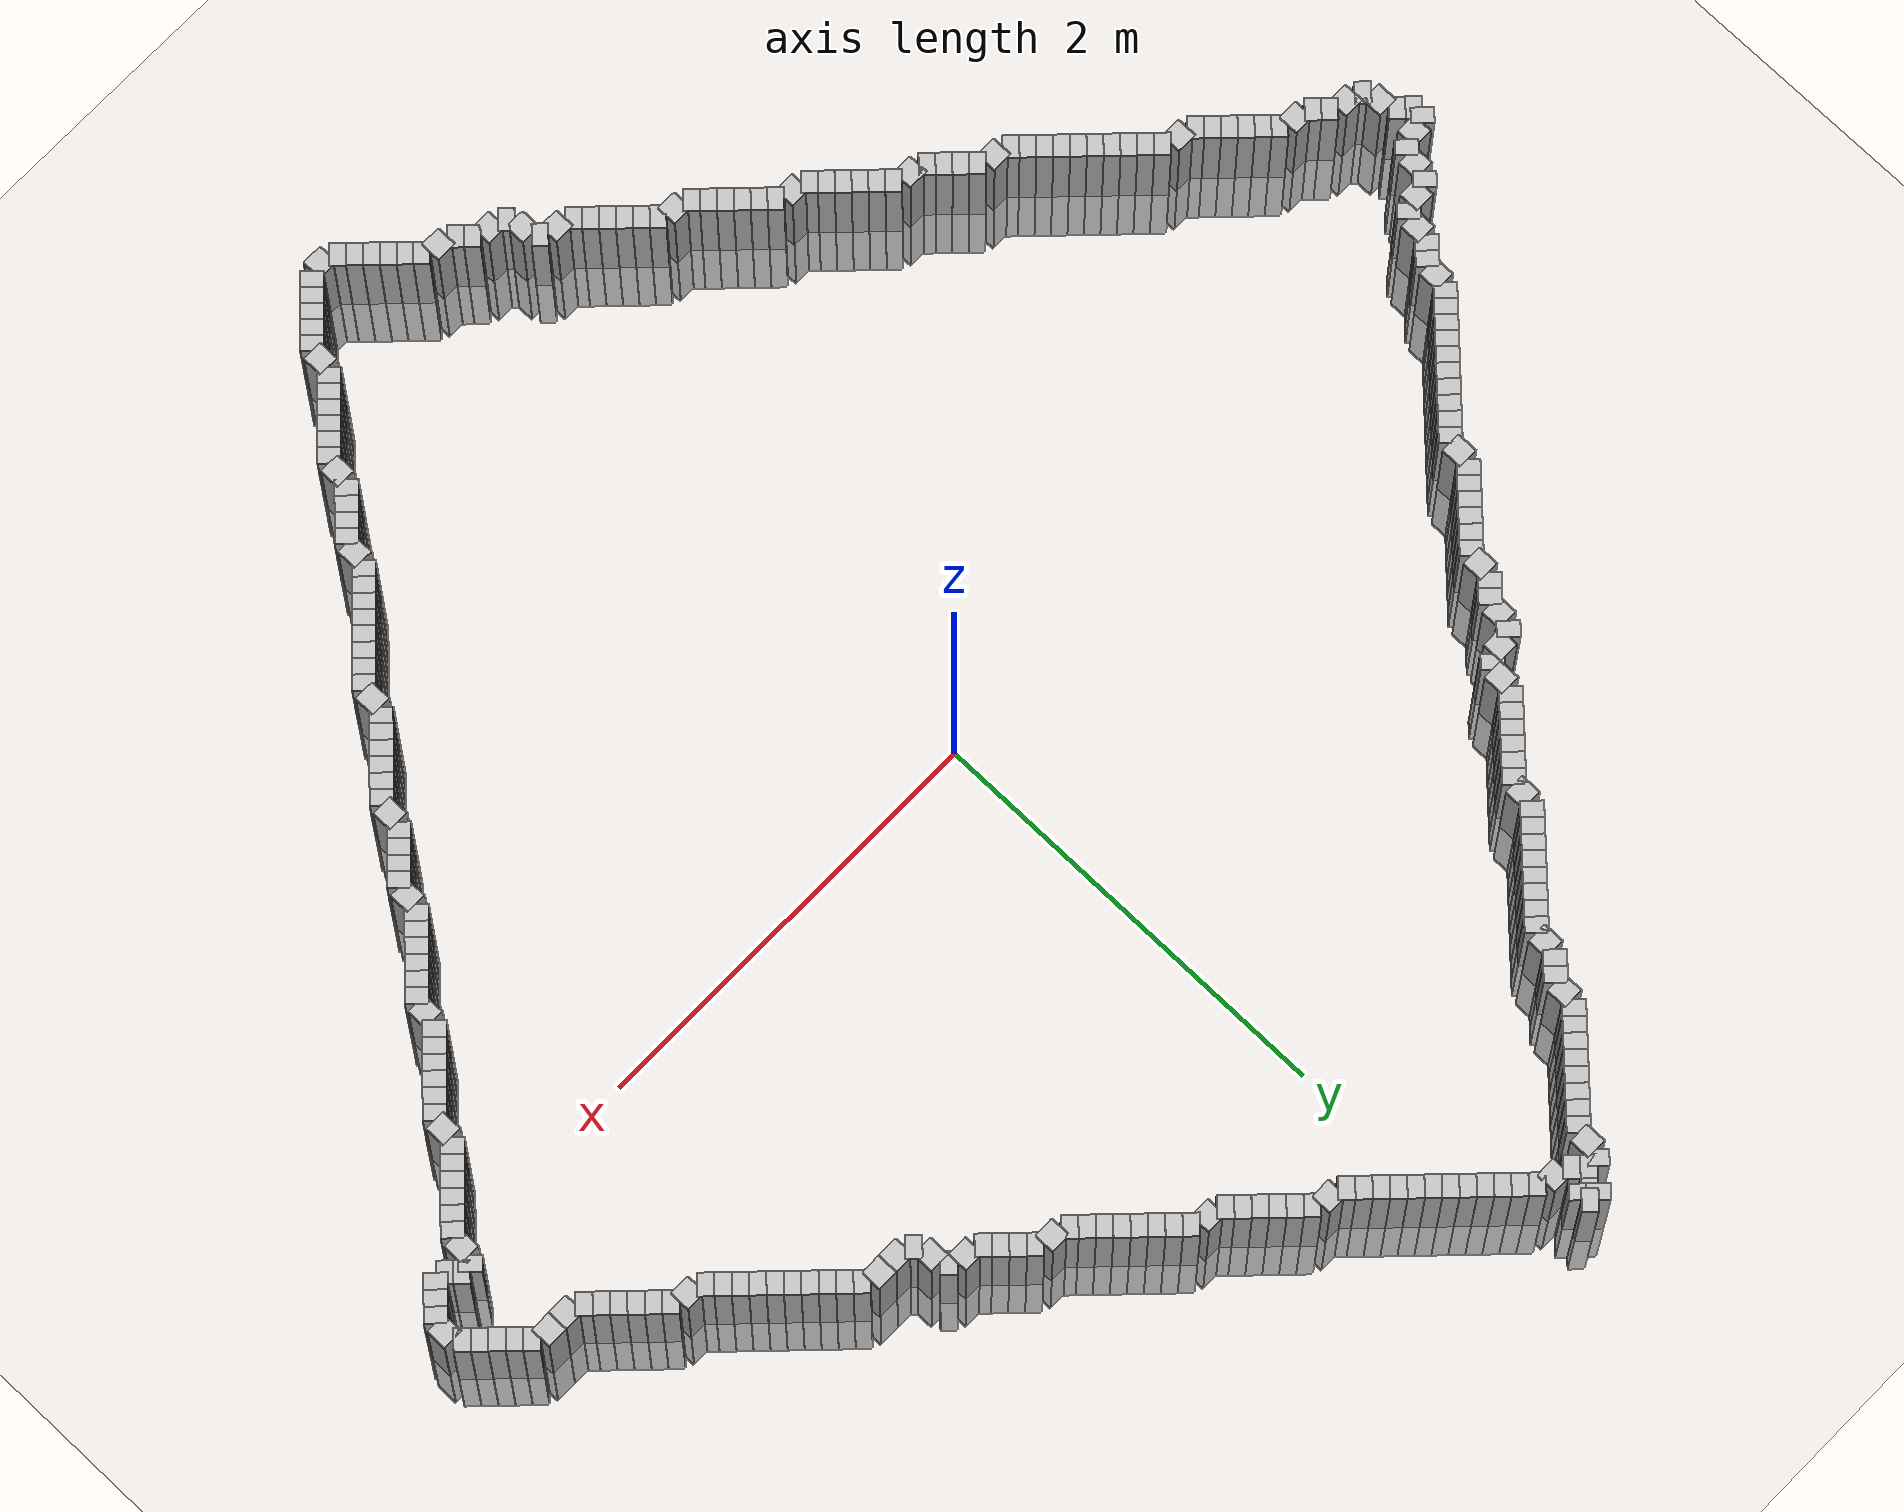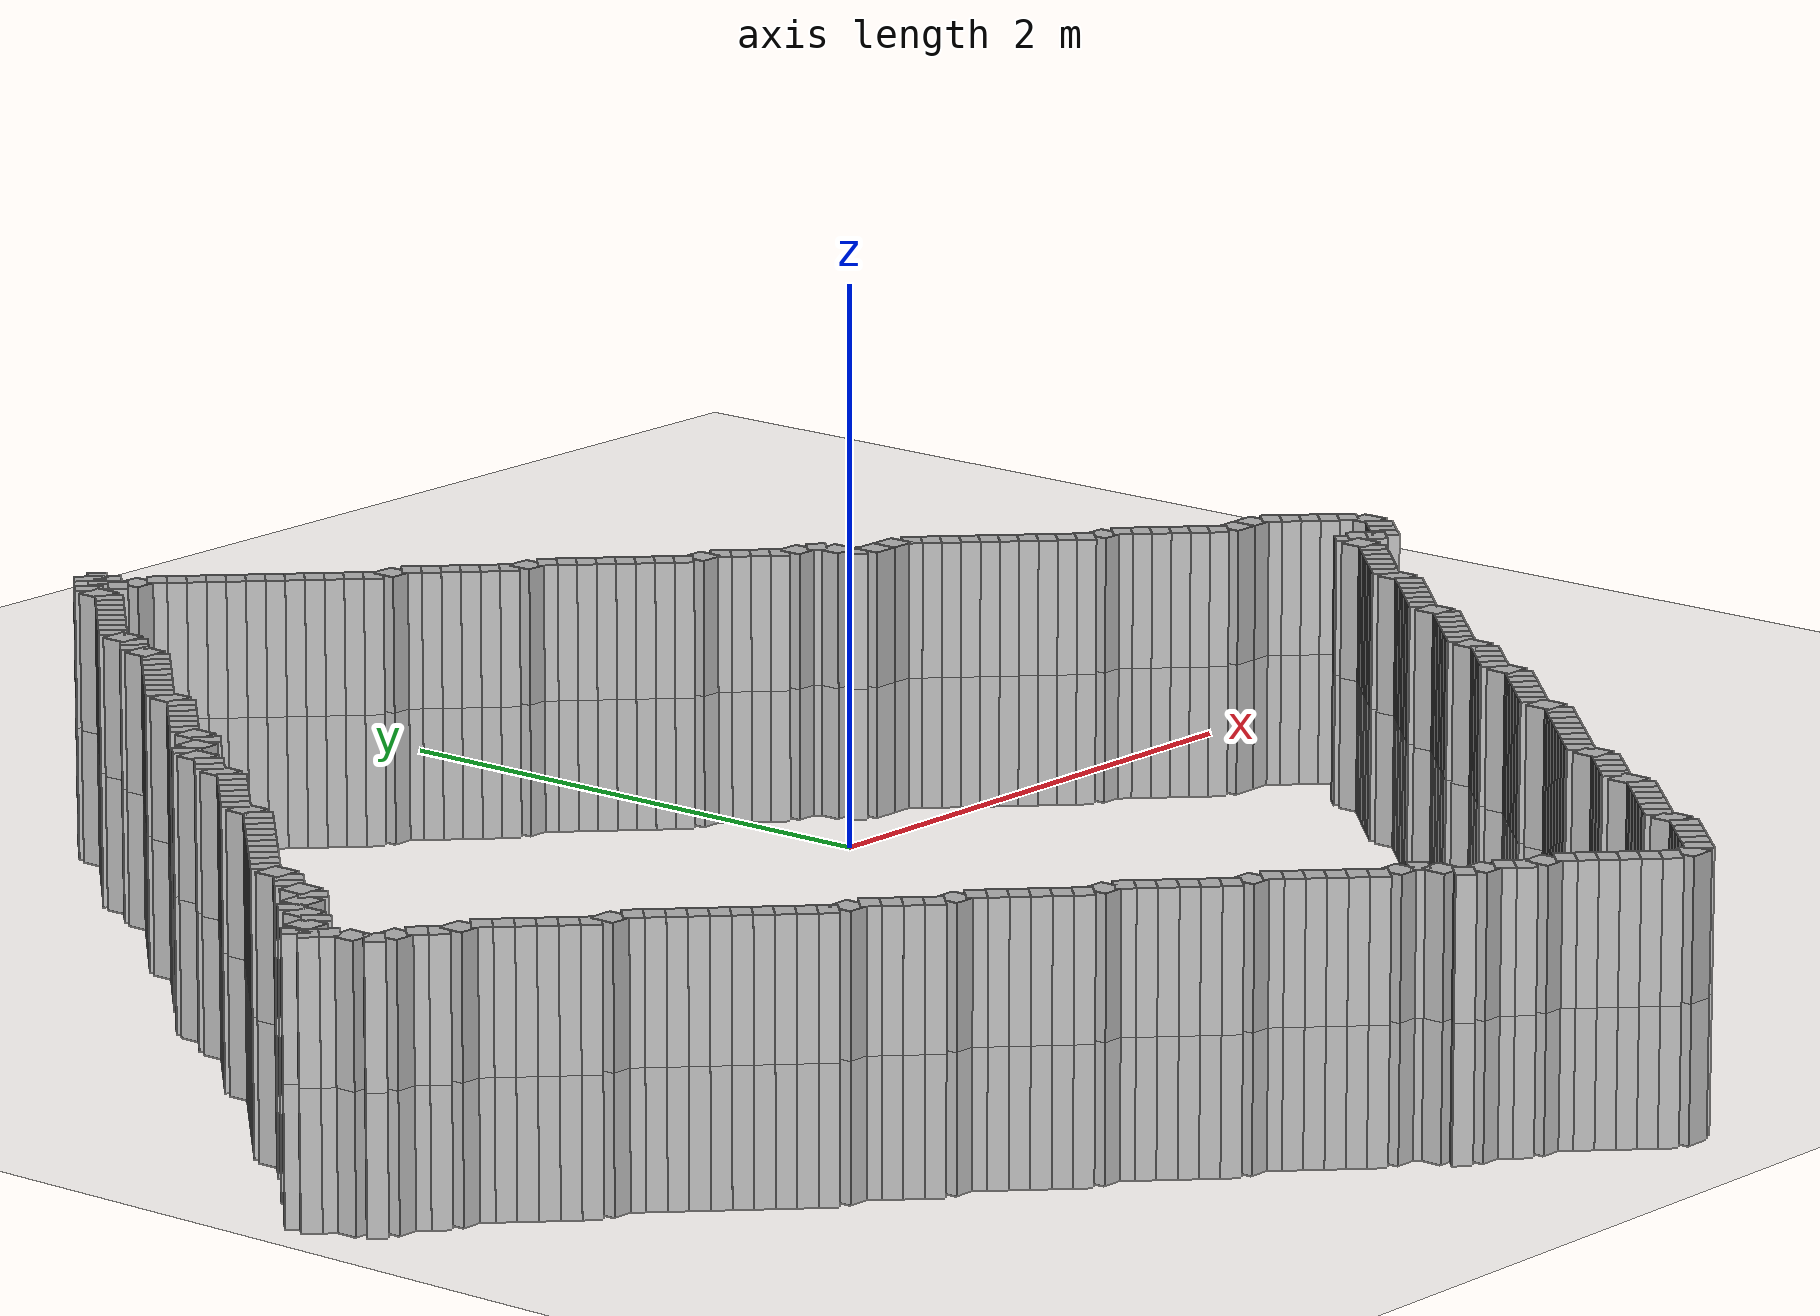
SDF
<?xml version="1.0" ?>
<!-- Gerado em 2025-04-29 22:05:05 -->
<sdf version="1.6">
  <world name="default">
    <include><uri>model://ground_plane</uri></include>
    <include><uri>model://sun</uri></include>

    <model name="wall_0">
      <static>true</static>
      <pose>0.2750 -3.2250 0 0 0 2.3562</pose>
      <link name="link">
        <visual name="vis">
          <geometry><box><size>0.0707 0.10 1.00</size></box></geometry>
        </visual>
        <collision name="col">
          <geometry><box><size>0.0707 0.10 1.00</size></box></geometry>
        </collision>
      </link>
    </model>

    <model name="wall_1">
      <static>true</static>
      <pose>0.2250 -3.1750 0 0 0 2.3562</pose>
      <link name="link">
        <visual name="vis">
          <geometry><box><size>0.0707 0.10 1.00</size></box></geometry>
        </visual>
        <collision name="col">
          <geometry><box><size>0.0707 0.10 1.00</size></box></geometry>
        </collision>
      </link>
    </model>

    <model name="wall_2">
      <static>true</static>
      <pose>0.1750 -3.1250 0 0 0 2.3562</pose>
      <link name="link">
        <visual name="vis">
          <geometry><box><size>0.0707 0.10 1.00</size></box></geometry>
        </visual>
        <collision name="col">
          <geometry><box><size>0.0707 0.10 1.00</size></box></geometry>
        </collision>
      </link>
    </model>

    <model name="wall_3">
      <static>true</static>
      <pose>0.1250 -3.0750 0 0 0 2.3562</pose>
      <link name="link">
        <visual name="vis">
          <geometry><box><size>0.0707 0.10 1.00</size></box></geometry>
        </visual>
        <collision name="col">
          <geometry><box><size>0.0707 0.10 1.00</size></box></geometry>
        </collision>
      </link>
    </model>

    <model name="wall_4">
      <static>true</static>
      <pose>0.0750 -3.0250 0 0 0 2.3562</pose>
      <link name="link">
        <visual name="vis">
          <geometry><box><size>0.0707 0.10 1.00</size></box></geometry>
        </visual>
        <collision name="col">
          <geometry><box><size>0.0707 0.10 1.00</size></box></geometry>
        </collision>
      </link>
    </model>

    <model name="wall_5">
      <static>true</static>
      <pose>0.0000 -3.0000 0 0 0 3.1416</pose>
      <link name="link">
        <visual name="vis">
          <geometry><box><size>0.1000 0.10 1.00</size></box></geometry>
        </visual>
        <collision name="col">
          <geometry><box><size>0.1000 0.10 1.00</size></box></geometry>
        </collision>
      </link>
    </model>

    <model name="wall_6">
      <static>true</static>
      <pose>-0.0750 -2.9750 0 0 0 2.3562</pose>
      <link name="link">
        <visual name="vis">
          <geometry><box><size>0.0707 0.10 1.00</size></box></geometry>
        </visual>
        <collision name="col">
          <geometry><box><size>0.0707 0.10 1.00</size></box></geometry>
        </collision>
      </link>
    </model>

    <model name="wall_7">
      <static>true</static>
      <pose>-0.1250 -2.9250 0 0 0 2.3562</pose>
      <link name="link">
        <visual name="vis">
          <geometry><box><size>0.0707 0.10 1.00</size></box></geometry>
        </visual>
        <collision name="col">
          <geometry><box><size>0.0707 0.10 1.00</size></box></geometry>
        </collision>
      </link>
    </model>

    <model name="wall_8">
      <static>true</static>
      <pose>-0.2000 -2.9000 0 0 0 3.1416</pose>
      <link name="link">
        <visual name="vis">
          <geometry><box><size>0.1000 0.10 1.00</size></box></geometry>
        </visual>
        <collision name="col">
          <geometry><box><size>0.1000 0.10 1.00</size></box></geometry>
        </collision>
      </link>
    </model>

    <model name="wall_9">
      <static>true</static>
      <pose>-0.2750 -2.8750 0 0 0 2.3562</pose>
      <link name="link">
        <visual name="vis">
          <geometry><box><size>0.0707 0.10 1.00</size></box></geometry>
        </visual>
        <collision name="col">
          <geometry><box><size>0.0707 0.10 1.00</size></box></geometry>
        </collision>
      </link>
    </model>

    <model name="wall_10">
      <static>true</static>
      <pose>-0.3000 -2.8000 0 0 0 1.5708</pose>
      <link name="link">
        <visual name="vis">
          <geometry><box><size>0.1000 0.10 1.00</size></box></geometry>
        </visual>
        <collision name="col">
          <geometry><box><size>0.1000 0.10 1.00</size></box></geometry>
        </collision>
      </link>
    </model>

    <model name="wall_11">
      <static>true</static>
      <pose>-0.3250 -2.7250 0 0 0 2.3562</pose>
      <link name="link">
        <visual name="vis">
          <geometry><box><size>0.0707 0.10 1.00</size></box></geometry>
        </visual>
        <collision name="col">
          <geometry><box><size>0.0707 0.10 1.00</size></box></geometry>
        </collision>
      </link>
    </model>

    <model name="wall_12">
      <static>true</static>
      <pose>-0.4000 -2.7000 0 0 0 3.1416</pose>
      <link name="link">
        <visual name="vis">
          <geometry><box><size>0.1000 0.10 1.00</size></box></geometry>
        </visual>
        <collision name="col">
          <geometry><box><size>0.1000 0.10 1.00</size></box></geometry>
        </collision>
      </link>
    </model>

    <model name="wall_13">
      <static>true</static>
      <pose>-0.4750 -2.6750 0 0 0 2.3562</pose>
      <link name="link">
        <visual name="vis">
          <geometry><box><size>0.0707 0.10 1.00</size></box></geometry>
        </visual>
        <collision name="col">
          <geometry><box><size>0.0707 0.10 1.00</size></box></geometry>
        </collision>
      </link>
    </model>

    <model name="wall_14">
      <static>true</static>
      <pose>-0.5250 -2.6250 0 0 0 2.3562</pose>
      <link name="link">
        <visual name="vis">
          <geometry><box><size>0.0707 0.10 1.00</size></box></geometry>
        </visual>
        <collision name="col">
          <geometry><box><size>0.0707 0.10 1.00</size></box></geometry>
        </collision>
      </link>
    </model>

    <model name="wall_15">
      <static>true</static>
      <pose>-0.5750 -2.5750 0 0 0 2.3562</pose>
      <link name="link">
        <visual name="vis">
          <geometry><box><size>0.0707 0.10 1.00</size></box></geometry>
        </visual>
        <collision name="col">
          <geometry><box><size>0.0707 0.10 1.00</size></box></geometry>
        </collision>
      </link>
    </model>

    <model name="wall_16">
      <static>true</static>
      <pose>-0.6250 -2.5250 0 0 0 2.3562</pose>
      <link name="link">
        <visual name="vis">
          <geometry><box><size>0.0707 0.10 1.00</size></box></geometry>
        </visual>
        <collision name="col">
          <geometry><box><size>0.0707 0.10 1.00</size></box></geometry>
        </collision>
      </link>
    </model>

    <model name="wall_17">
      <static>true</static>
      <pose>-0.6750 -2.4750 0 0 0 2.3562</pose>
      <link name="link">
        <visual name="vis">
          <geometry><box><size>0.0707 0.10 1.00</size></box></geometry>
        </visual>
        <collision name="col">
          <geometry><box><size>0.0707 0.10 1.00</size></box></geometry>
        </collision>
      </link>
    </model>

    <model name="wall_18">
      <static>true</static>
      <pose>-0.7250 -2.4250 0 0 0 2.3562</pose>
      <link name="link">
        <visual name="vis">
          <geometry><box><size>0.0707 0.10 1.00</size></box></geometry>
        </visual>
        <collision name="col">
          <geometry><box><size>0.0707 0.10 1.00</size></box></geometry>
        </collision>
      </link>
    </model>

    <model name="wall_19">
      <static>true</static>
      <pose>-0.8000 -2.4000 0 0 0 3.1416</pose>
      <link name="link">
        <visual name="vis">
          <geometry><box><size>0.1000 0.10 1.00</size></box></geometry>
        </visual>
        <collision name="col">
          <geometry><box><size>0.1000 0.10 1.00</size></box></geometry>
        </collision>
      </link>
    </model>

    <model name="wall_20">
      <static>true</static>
      <pose>-0.8750 -2.3750 0 0 0 2.3562</pose>
      <link name="link">
        <visual name="vis">
          <geometry><box><size>0.0707 0.10 1.00</size></box></geometry>
        </visual>
        <collision name="col">
          <geometry><box><size>0.0707 0.10 1.00</size></box></geometry>
        </collision>
      </link>
    </model>

    <model name="wall_21">
      <static>true</static>
      <pose>-0.9250 -2.3250 0 0 0 2.3562</pose>
      <link name="link">
        <visual name="vis">
          <geometry><box><size>0.0707 0.10 1.00</size></box></geometry>
        </visual>
        <collision name="col">
          <geometry><box><size>0.0707 0.10 1.00</size></box></geometry>
        </collision>
      </link>
    </model>

    <model name="wall_22">
      <static>true</static>
      <pose>-0.9750 -2.2750 0 0 0 2.3562</pose>
      <link name="link">
        <visual name="vis">
          <geometry><box><size>0.0707 0.10 1.00</size></box></geometry>
        </visual>
        <collision name="col">
          <geometry><box><size>0.0707 0.10 1.00</size></box></geometry>
        </collision>
      </link>
    </model>

    <model name="wall_23">
      <static>true</static>
      <pose>-1.0250 -2.2250 0 0 0 2.3562</pose>
      <link name="link">
        <visual name="vis">
          <geometry><box><size>0.0707 0.10 1.00</size></box></geometry>
        </visual>
        <collision name="col">
          <geometry><box><size>0.0707 0.10 1.00</size></box></geometry>
        </collision>
      </link>
    </model>

    <model name="wall_24">
      <static>true</static>
      <pose>-1.0750 -2.1750 0 0 0 2.3562</pose>
      <link name="link">
        <visual name="vis">
          <geometry><box><size>0.0707 0.10 1.00</size></box></geometry>
        </visual>
        <collision name="col">
          <geometry><box><size>0.0707 0.10 1.00</size></box></geometry>
        </collision>
      </link>
    </model>

    <model name="wall_25">
      <static>true</static>
      <pose>-1.1250 -2.1250 0 0 0 2.3562</pose>
      <link name="link">
        <visual name="vis">
          <geometry><box><size>0.0707 0.10 1.00</size></box></geometry>
        </visual>
        <collision name="col">
          <geometry><box><size>0.0707 0.10 1.00</size></box></geometry>
        </collision>
      </link>
    </model>

    <model name="wall_26">
      <static>true</static>
      <pose>-1.2000 -2.1000 0 0 0 3.1416</pose>
      <link name="link">
        <visual name="vis">
          <geometry><box><size>0.1000 0.10 1.00</size></box></geometry>
        </visual>
        <collision name="col">
          <geometry><box><size>0.1000 0.10 1.00</size></box></geometry>
        </collision>
      </link>
    </model>

    <model name="wall_27">
      <static>true</static>
      <pose>-1.2750 -2.0750 0 0 0 2.3562</pose>
      <link name="link">
        <visual name="vis">
          <geometry><box><size>0.0707 0.10 1.00</size></box></geometry>
        </visual>
        <collision name="col">
          <geometry><box><size>0.0707 0.10 1.00</size></box></geometry>
        </collision>
      </link>
    </model>

    <model name="wall_28">
      <static>true</static>
      <pose>-1.3250 -2.0250 0 0 0 2.3562</pose>
      <link name="link">
        <visual name="vis">
          <geometry><box><size>0.0707 0.10 1.00</size></box></geometry>
        </visual>
        <collision name="col">
          <geometry><box><size>0.0707 0.10 1.00</size></box></geometry>
        </collision>
      </link>
    </model>

    <model name="wall_29">
      <static>true</static>
      <pose>-1.3750 -1.9750 0 0 0 2.3562</pose>
      <link name="link">
        <visual name="vis">
          <geometry><box><size>0.0707 0.10 1.00</size></box></geometry>
        </visual>
        <collision name="col">
          <geometry><box><size>0.0707 0.10 1.00</size></box></geometry>
        </collision>
      </link>
    </model>

    <model name="wall_30">
      <static>true</static>
      <pose>-1.4250 -1.9250 0 0 0 2.3562</pose>
      <link name="link">
        <visual name="vis">
          <geometry><box><size>0.0707 0.10 1.00</size></box></geometry>
        </visual>
        <collision name="col">
          <geometry><box><size>0.0707 0.10 1.00</size></box></geometry>
        </collision>
      </link>
    </model>

    <model name="wall_31">
      <static>true</static>
      <pose>-1.4750 -1.8750 0 0 0 2.3562</pose>
      <link name="link">
        <visual name="vis">
          <geometry><box><size>0.0707 0.10 1.00</size></box></geometry>
        </visual>
        <collision name="col">
          <geometry><box><size>0.0707 0.10 1.00</size></box></geometry>
        </collision>
      </link>
    </model>

    <model name="wall_32">
      <static>true</static>
      <pose>-1.5250 -1.8250 0 0 0 2.3562</pose>
      <link name="link">
        <visual name="vis">
          <geometry><box><size>0.0707 0.10 1.00</size></box></geometry>
        </visual>
        <collision name="col">
          <geometry><box><size>0.0707 0.10 1.00</size></box></geometry>
        </collision>
      </link>
    </model>

    <model name="wall_33">
      <static>true</static>
      <pose>-1.6000 -1.8000 0 0 0 3.1416</pose>
      <link name="link">
        <visual name="vis">
          <geometry><box><size>0.1000 0.10 1.00</size></box></geometry>
        </visual>
        <collision name="col">
          <geometry><box><size>0.1000 0.10 1.00</size></box></geometry>
        </collision>
      </link>
    </model>

    <model name="wall_34">
      <static>true</static>
      <pose>-1.6750 -1.7750 0 0 0 2.3562</pose>
      <link name="link">
        <visual name="vis">
          <geometry><box><size>0.0707 0.10 1.00</size></box></geometry>
        </visual>
        <collision name="col">
          <geometry><box><size>0.0707 0.10 1.00</size></box></geometry>
        </collision>
      </link>
    </model>

    <model name="wall_35">
      <static>true</static>
      <pose>-1.7250 -1.7250 0 0 0 2.3562</pose>
      <link name="link">
        <visual name="vis">
          <geometry><box><size>0.0707 0.10 1.00</size></box></geometry>
        </visual>
        <collision name="col">
          <geometry><box><size>0.0707 0.10 1.00</size></box></geometry>
        </collision>
      </link>
    </model>

    <model name="wall_36">
      <static>true</static>
      <pose>-1.7750 -1.6750 0 0 0 2.3562</pose>
      <link name="link">
        <visual name="vis">
          <geometry><box><size>0.0707 0.10 1.00</size></box></geometry>
        </visual>
        <collision name="col">
          <geometry><box><size>0.0707 0.10 1.00</size></box></geometry>
        </collision>
      </link>
    </model>

    <model name="wall_37">
      <static>true</static>
      <pose>-1.8250 -1.6250 0 0 0 2.3562</pose>
      <link name="link">
        <visual name="vis">
          <geometry><box><size>0.0707 0.10 1.00</size></box></geometry>
        </visual>
        <collision name="col">
          <geometry><box><size>0.0707 0.10 1.00</size></box></geometry>
        </collision>
      </link>
    </model>

    <model name="wall_38">
      <static>true</static>
      <pose>-1.9000 -1.6000 0 0 0 3.1416</pose>
      <link name="link">
        <visual name="vis">
          <geometry><box><size>0.1000 0.10 1.00</size></box></geometry>
        </visual>
        <collision name="col">
          <geometry><box><size>0.1000 0.10 1.00</size></box></geometry>
        </collision>
      </link>
    </model>

    <model name="wall_39">
      <static>true</static>
      <pose>-1.9750 -1.5750 0 0 0 2.3562</pose>
      <link name="link">
        <visual name="vis">
          <geometry><box><size>0.0707 0.10 1.00</size></box></geometry>
        </visual>
        <collision name="col">
          <geometry><box><size>0.0707 0.10 1.00</size></box></geometry>
        </collision>
      </link>
    </model>

    <model name="wall_40">
      <static>true</static>
      <pose>-2.0250 -1.5250 0 0 0 2.3562</pose>
      <link name="link">
        <visual name="vis">
          <geometry><box><size>0.0707 0.10 1.00</size></box></geometry>
        </visual>
        <collision name="col">
          <geometry><box><size>0.0707 0.10 1.00</size></box></geometry>
        </collision>
      </link>
    </model>

    <model name="wall_41">
      <static>true</static>
      <pose>-2.0750 -1.4750 0 0 0 2.3562</pose>
      <link name="link">
        <visual name="vis">
          <geometry><box><size>0.0707 0.10 1.00</size></box></geometry>
        </visual>
        <collision name="col">
          <geometry><box><size>0.0707 0.10 1.00</size></box></geometry>
        </collision>
      </link>
    </model>

    <model name="wall_42">
      <static>true</static>
      <pose>-2.1250 -1.4250 0 0 0 2.3562</pose>
      <link name="link">
        <visual name="vis">
          <geometry><box><size>0.0707 0.10 1.00</size></box></geometry>
        </visual>
        <collision name="col">
          <geometry><box><size>0.0707 0.10 1.00</size></box></geometry>
        </collision>
      </link>
    </model>

    <model name="wall_43">
      <static>true</static>
      <pose>-2.1750 -1.3750 0 0 0 2.3562</pose>
      <link name="link">
        <visual name="vis">
          <geometry><box><size>0.0707 0.10 1.00</size></box></geometry>
        </visual>
        <collision name="col">
          <geometry><box><size>0.0707 0.10 1.00</size></box></geometry>
        </collision>
      </link>
    </model>

    <model name="wall_44">
      <static>true</static>
      <pose>-2.2250 -1.3250 0 0 0 2.3562</pose>
      <link name="link">
        <visual name="vis">
          <geometry><box><size>0.0707 0.10 1.00</size></box></geometry>
        </visual>
        <collision name="col">
          <geometry><box><size>0.0707 0.10 1.00</size></box></geometry>
        </collision>
      </link>
    </model>

    <model name="wall_45">
      <static>true</static>
      <pose>-2.2750 -1.2750 0 0 0 2.3562</pose>
      <link name="link">
        <visual name="vis">
          <geometry><box><size>0.0707 0.10 1.00</size></box></geometry>
        </visual>
        <collision name="col">
          <geometry><box><size>0.0707 0.10 1.00</size></box></geometry>
        </collision>
      </link>
    </model>

    <model name="wall_46">
      <static>true</static>
      <pose>-2.3250 -1.2250 0 0 0 2.3562</pose>
      <link name="link">
        <visual name="vis">
          <geometry><box><size>0.0707 0.10 1.00</size></box></geometry>
        </visual>
        <collision name="col">
          <geometry><box><size>0.0707 0.10 1.00</size></box></geometry>
        </collision>
      </link>
    </model>

    <model name="wall_47">
      <static>true</static>
      <pose>-2.3750 -1.1750 0 0 0 2.3562</pose>
      <link name="link">
        <visual name="vis">
          <geometry><box><size>0.0707 0.10 1.00</size></box></geometry>
        </visual>
        <collision name="col">
          <geometry><box><size>0.0707 0.10 1.00</size></box></geometry>
        </collision>
      </link>
    </model>

    <model name="wall_48">
      <static>true</static>
      <pose>-2.4250 -1.1250 0 0 0 2.3562</pose>
      <link name="link">
        <visual name="vis">
          <geometry><box><size>0.0707 0.10 1.00</size></box></geometry>
        </visual>
        <collision name="col">
          <geometry><box><size>0.0707 0.10 1.00</size></box></geometry>
        </collision>
      </link>
    </model>

    <model name="wall_49">
      <static>true</static>
      <pose>-2.5000 -1.1000 0 0 0 3.1416</pose>
      <link name="link">
        <visual name="vis">
          <geometry><box><size>0.1000 0.10 1.00</size></box></geometry>
        </visual>
        <collision name="col">
          <geometry><box><size>0.1000 0.10 1.00</size></box></geometry>
        </collision>
      </link>
    </model>

    <model name="wall_50">
      <static>true</static>
      <pose>-2.5750 -1.0750 0 0 0 2.3562</pose>
      <link name="link">
        <visual name="vis">
          <geometry><box><size>0.0707 0.10 1.00</size></box></geometry>
        </visual>
        <collision name="col">
          <geometry><box><size>0.0707 0.10 1.00</size></box></geometry>
        </collision>
      </link>
    </model>

    <model name="wall_51">
      <static>true</static>
      <pose>-2.6250 -1.0250 0 0 0 2.3562</pose>
      <link name="link">
        <visual name="vis">
          <geometry><box><size>0.0707 0.10 1.00</size></box></geometry>
        </visual>
        <collision name="col">
          <geometry><box><size>0.0707 0.10 1.00</size></box></geometry>
        </collision>
      </link>
    </model>

    <model name="wall_52">
      <static>true</static>
      <pose>-2.6750 -0.9750 0 0 0 2.3562</pose>
      <link name="link">
        <visual name="vis">
          <geometry><box><size>0.0707 0.10 1.00</size></box></geometry>
        </visual>
        <collision name="col">
          <geometry><box><size>0.0707 0.10 1.00</size></box></geometry>
        </collision>
      </link>
    </model>

    <model name="wall_53">
      <static>true</static>
      <pose>-2.7250 -0.9250 0 0 0 2.3562</pose>
      <link name="link">
        <visual name="vis">
          <geometry><box><size>0.0707 0.10 1.00</size></box></geometry>
        </visual>
        <collision name="col">
          <geometry><box><size>0.0707 0.10 1.00</size></box></geometry>
        </collision>
      </link>
    </model>

    <model name="wall_54">
      <static>true</static>
      <pose>-2.7750 -0.8750 0 0 0 2.3562</pose>
      <link name="link">
        <visual name="vis">
          <geometry><box><size>0.0707 0.10 1.00</size></box></geometry>
        </visual>
        <collision name="col">
          <geometry><box><size>0.0707 0.10 1.00</size></box></geometry>
        </collision>
      </link>
    </model>

    <model name="wall_55">
      <static>true</static>
      <pose>-2.8250 -0.8250 0 0 0 2.3562</pose>
      <link name="link">
        <visual name="vis">
          <geometry><box><size>0.0707 0.10 1.00</size></box></geometry>
        </visual>
        <collision name="col">
          <geometry><box><size>0.0707 0.10 1.00</size></box></geometry>
        </collision>
      </link>
    </model>

    <model name="wall_56">
      <static>true</static>
      <pose>-2.9000 -0.8000 0 0 0 3.1416</pose>
      <link name="link">
        <visual name="vis">
          <geometry><box><size>0.1000 0.10 1.00</size></box></geometry>
        </visual>
        <collision name="col">
          <geometry><box><size>0.1000 0.10 1.00</size></box></geometry>
        </collision>
      </link>
    </model>

    <model name="wall_57">
      <static>true</static>
      <pose>-2.9750 -0.7750 0 0 0 2.3562</pose>
      <link name="link">
        <visual name="vis">
          <geometry><box><size>0.0707 0.10 1.00</size></box></geometry>
        </visual>
        <collision name="col">
          <geometry><box><size>0.0707 0.10 1.00</size></box></geometry>
        </collision>
      </link>
    </model>

    <model name="wall_58">
      <static>true</static>
      <pose>-3.0250 -0.7250 0 0 0 2.3562</pose>
      <link name="link">
        <visual name="vis">
          <geometry><box><size>0.0707 0.10 1.00</size></box></geometry>
        </visual>
        <collision name="col">
          <geometry><box><size>0.0707 0.10 1.00</size></box></geometry>
        </collision>
      </link>
    </model>

    <model name="wall_59">
      <static>true</static>
      <pose>-3.1000 -0.7000 0 0 0 3.1416</pose>
      <link name="link">
        <visual name="vis">
          <geometry><box><size>0.1000 0.10 1.00</size></box></geometry>
        </visual>
        <collision name="col">
          <geometry><box><size>0.1000 0.10 1.00</size></box></geometry>
        </collision>
      </link>
    </model>

    <model name="wall_60">
      <static>true</static>
      <pose>-3.1750 -0.6750 0 0 0 2.3562</pose>
      <link name="link">
        <visual name="vis">
          <geometry><box><size>0.0707 0.10 1.00</size></box></geometry>
        </visual>
        <collision name="col">
          <geometry><box><size>0.0707 0.10 1.00</size></box></geometry>
        </collision>
      </link>
    </model>

    <model name="wall_61">
      <static>true</static>
      <pose>-3.2000 -0.6000 0 0 0 1.5708</pose>
      <link name="link">
        <visual name="vis">
          <geometry><box><size>0.1000 0.10 1.00</size></box></geometry>
        </visual>
        <collision name="col">
          <geometry><box><size>0.1000 0.10 1.00</size></box></geometry>
        </collision>
      </link>
    </model>

    <model name="wall_62">
      <static>true</static>
      <pose>-3.2250 -0.5250 0 0 0 2.3562</pose>
      <link name="link">
        <visual name="vis">
          <geometry><box><size>0.0707 0.10 1.00</size></box></geometry>
        </visual>
        <collision name="col">
          <geometry><box><size>0.0707 0.10 1.00</size></box></geometry>
        </collision>
      </link>
    </model>

    <model name="wall_63">
      <static>true</static>
      <pose>-3.2750 -0.4750 0 0 0 2.3562</pose>
      <link name="link">
        <visual name="vis">
          <geometry><box><size>0.0707 0.10 1.00</size></box></geometry>
        </visual>
        <collision name="col">
          <geometry><box><size>0.0707 0.10 1.00</size></box></geometry>
        </collision>
      </link>
    </model>

    <model name="wall_64">
      <static>true</static>
      <pose>-3.2750 -0.4250 0 0 0 0.7854</pose>
      <link name="link">
        <visual name="vis">
          <geometry><box><size>0.0707 0.10 1.00</size></box></geometry>
        </visual>
        <collision name="col">
          <geometry><box><size>0.0707 0.10 1.00</size></box></geometry>
        </collision>
      </link>
    </model>

    <model name="wall_65">
      <static>true</static>
      <pose>-3.2000 -0.4000 0 0 0 0.0000</pose>
      <link name="link">
        <visual name="vis">
          <geometry><box><size>0.1000 0.10 1.00</size></box></geometry>
        </visual>
        <collision name="col">
          <geometry><box><size>0.1000 0.10 1.00</size></box></geometry>
        </collision>
      </link>
    </model>

    <model name="wall_66">
      <static>true</static>
      <pose>-3.1250 -0.3750 0 0 0 0.7854</pose>
      <link name="link">
        <visual name="vis">
          <geometry><box><size>0.0707 0.10 1.00</size></box></geometry>
        </visual>
        <collision name="col">
          <geometry><box><size>0.0707 0.10 1.00</size></box></geometry>
        </collision>
      </link>
    </model>

    <model name="wall_67">
      <static>true</static>
      <pose>-3.1000 -0.3000 0 0 0 1.5708</pose>
      <link name="link">
        <visual name="vis">
          <geometry><box><size>0.1000 0.10 1.00</size></box></geometry>
        </visual>
        <collision name="col">
          <geometry><box><size>0.1000 0.10 1.00</size></box></geometry>
        </collision>
      </link>
    </model>

    <model name="wall_68">
      <static>true</static>
      <pose>-3.0750 -0.2250 0 0 0 0.7854</pose>
      <link name="link">
        <visual name="vis">
          <geometry><box><size>0.0707 0.10 1.00</size></box></geometry>
        </visual>
        <collision name="col">
          <geometry><box><size>0.0707 0.10 1.00</size></box></geometry>
        </collision>
      </link>
    </model>

    <model name="wall_69">
      <static>true</static>
      <pose>-3.0000 -0.2000 0 0 0 0.0000</pose>
      <link name="link">
        <visual name="vis">
          <geometry><box><size>0.1000 0.10 1.00</size></box></geometry>
        </visual>
        <collision name="col">
          <geometry><box><size>0.1000 0.10 1.00</size></box></geometry>
        </collision>
      </link>
    </model>

    <model name="wall_70">
      <static>true</static>
      <pose>-2.9250 -0.1750 0 0 0 0.7854</pose>
      <link name="link">
        <visual name="vis">
          <geometry><box><size>0.0707 0.10 1.00</size></box></geometry>
        </visual>
        <collision name="col">
          <geometry><box><size>0.0707 0.10 1.00</size></box></geometry>
        </collision>
      </link>
    </model>

    <model name="wall_71">
      <static>true</static>
      <pose>-2.9000 -0.1000 0 0 0 1.5708</pose>
      <link name="link">
        <visual name="vis">
          <geometry><box><size>0.1000 0.10 1.00</size></box></geometry>
        </visual>
        <collision name="col">
          <geometry><box><size>0.1000 0.10 1.00</size></box></geometry>
        </collision>
      </link>
    </model>

    <model name="wall_72">
      <static>true</static>
      <pose>-2.8750 -0.0250 0 0 0 0.7854</pose>
      <link name="link">
        <visual name="vis">
          <geometry><box><size>0.0707 0.10 1.00</size></box></geometry>
        </visual>
        <collision name="col">
          <geometry><box><size>0.0707 0.10 1.00</size></box></geometry>
        </collision>
      </link>
    </model>

    <model name="wall_73">
      <static>true</static>
      <pose>-2.8250 0.0250 0 0 0 0.7854</pose>
      <link name="link">
        <visual name="vis">
          <geometry><box><size>0.0707 0.10 1.00</size></box></geometry>
        </visual>
        <collision name="col">
          <geometry><box><size>0.0707 0.10 1.00</size></box></geometry>
        </collision>
      </link>
    </model>

    <model name="wall_74">
      <static>true</static>
      <pose>-2.8000 0.1000 0 0 0 1.5708</pose>
      <link name="link">
        <visual name="vis">
          <geometry><box><size>0.1000 0.10 1.00</size></box></geometry>
        </visual>
        <collision name="col">
          <geometry><box><size>0.1000 0.10 1.00</size></box></geometry>
        </collision>
      </link>
    </model>

    <model name="wall_75">
      <static>true</static>
      <pose>-2.7750 0.1750 0 0 0 0.7854</pose>
      <link name="link">
        <visual name="vis">
          <geometry><box><size>0.0707 0.10 1.00</size></box></geometry>
        </visual>
        <collision name="col">
          <geometry><box><size>0.0707 0.10 1.00</size></box></geometry>
        </collision>
      </link>
    </model>

    <model name="wall_76">
      <static>true</static>
      <pose>-2.7250 0.2250 0 0 0 0.7854</pose>
      <link name="link">
        <visual name="vis">
          <geometry><box><size>0.0707 0.10 1.00</size></box></geometry>
        </visual>
        <collision name="col">
          <geometry><box><size>0.0707 0.10 1.00</size></box></geometry>
        </collision>
      </link>
    </model>

    <model name="wall_77">
      <static>true</static>
      <pose>-2.6750 0.2750 0 0 0 0.7854</pose>
      <link name="link">
        <visual name="vis">
          <geometry><box><size>0.0707 0.10 1.00</size></box></geometry>
        </visual>
        <collision name="col">
          <geometry><box><size>0.0707 0.10 1.00</size></box></geometry>
        </collision>
      </link>
    </model>

    <model name="wall_78">
      <static>true</static>
      <pose>-2.6250 0.3250 0 0 0 0.7854</pose>
      <link name="link">
        <visual name="vis">
          <geometry><box><size>0.0707 0.10 1.00</size></box></geometry>
        </visual>
        <collision name="col">
          <geometry><box><size>0.0707 0.10 1.00</size></box></geometry>
        </collision>
      </link>
    </model>

    <model name="wall_79">
      <static>true</static>
      <pose>-2.5750 0.3750 0 0 0 0.7854</pose>
      <link name="link">
        <visual name="vis">
          <geometry><box><size>0.0707 0.10 1.00</size></box></geometry>
        </visual>
        <collision name="col">
          <geometry><box><size>0.0707 0.10 1.00</size></box></geometry>
        </collision>
      </link>
    </model>

    <model name="wall_80">
      <static>true</static>
      <pose>-2.5250 0.4250 0 0 0 0.7854</pose>
      <link name="link">
        <visual name="vis">
          <geometry><box><size>0.0707 0.10 1.00</size></box></geometry>
        </visual>
        <collision name="col">
          <geometry><box><size>0.0707 0.10 1.00</size></box></geometry>
        </collision>
      </link>
    </model>

    <model name="wall_81">
      <static>true</static>
      <pose>-2.4750 0.4750 0 0 0 0.7854</pose>
      <link name="link">
        <visual name="vis">
          <geometry><box><size>0.0707 0.10 1.00</size></box></geometry>
        </visual>
        <collision name="col">
          <geometry><box><size>0.0707 0.10 1.00</size></box></geometry>
        </collision>
      </link>
    </model>

    <model name="wall_82">
      <static>true</static>
      <pose>-2.4250 0.5250 0 0 0 0.7854</pose>
      <link name="link">
        <visual name="vis">
          <geometry><box><size>0.0707 0.10 1.00</size></box></geometry>
        </visual>
        <collision name="col">
          <geometry><box><size>0.0707 0.10 1.00</size></box></geometry>
        </collision>
      </link>
    </model>

    <model name="wall_83">
      <static>true</static>
      <pose>-2.3750 0.5750 0 0 0 0.7854</pose>
      <link name="link">
        <visual name="vis">
          <geometry><box><size>0.0707 0.10 1.00</size></box></geometry>
        </visual>
        <collision name="col">
          <geometry><box><size>0.0707 0.10 1.00</size></box></geometry>
        </collision>
      </link>
    </model>

    <model name="wall_84">
      <static>true</static>
      <pose>-2.3250 0.6250 0 0 0 0.7854</pose>
      <link name="link">
        <visual name="vis">
          <geometry><box><size>0.0707 0.10 1.00</size></box></geometry>
        </visual>
        <collision name="col">
          <geometry><box><size>0.0707 0.10 1.00</size></box></geometry>
        </collision>
      </link>
    </model>

    <model name="wall_85">
      <static>true</static>
      <pose>-2.3000 0.7000 0 0 0 1.5708</pose>
      <link name="link">
        <visual name="vis">
          <geometry><box><size>0.1000 0.10 1.00</size></box></geometry>
        </visual>
        <collision name="col">
          <geometry><box><size>0.1000 0.10 1.00</size></box></geometry>
        </collision>
      </link>
    </model>

    <model name="wall_86">
      <static>true</static>
      <pose>-2.2750 0.7750 0 0 0 0.7854</pose>
      <link name="link">
        <visual name="vis">
          <geometry><box><size>0.0707 0.10 1.00</size></box></geometry>
        </visual>
        <collision name="col">
          <geometry><box><size>0.0707 0.10 1.00</size></box></geometry>
        </collision>
      </link>
    </model>

    <model name="wall_87">
      <static>true</static>
      <pose>-2.2250 0.8250 0 0 0 0.7854</pose>
      <link name="link">
        <visual name="vis">
          <geometry><box><size>0.0707 0.10 1.00</size></box></geometry>
        </visual>
        <collision name="col">
          <geometry><box><size>0.0707 0.10 1.00</size></box></geometry>
        </collision>
      </link>
    </model>

    <model name="wall_88">
      <static>true</static>
      <pose>-2.1750 0.8750 0 0 0 0.7854</pose>
      <link name="link">
        <visual name="vis">
          <geometry><box><size>0.0707 0.10 1.00</size></box></geometry>
        </visual>
        <collision name="col">
          <geometry><box><size>0.0707 0.10 1.00</size></box></geometry>
        </collision>
      </link>
    </model>

    <model name="wall_89">
      <static>true</static>
      <pose>-2.1250 0.9250 0 0 0 0.7854</pose>
      <link name="link">
        <visual name="vis">
          <geometry><box><size>0.0707 0.10 1.00</size></box></geometry>
        </visual>
        <collision name="col">
          <geometry><box><size>0.0707 0.10 1.00</size></box></geometry>
        </collision>
      </link>
    </model>

    <model name="wall_90">
      <static>true</static>
      <pose>-2.0750 0.9750 0 0 0 0.7854</pose>
      <link name="link">
        <visual name="vis">
          <geometry><box><size>0.0707 0.10 1.00</size></box></geometry>
        </visual>
        <collision name="col">
          <geometry><box><size>0.0707 0.10 1.00</size></box></geometry>
        </collision>
      </link>
    </model>

    <model name="wall_91">
      <static>true</static>
      <pose>-2.0250 1.0250 0 0 0 0.7854</pose>
      <link name="link">
        <visual name="vis">
          <geometry><box><size>0.0707 0.10 1.00</size></box></geometry>
        </visual>
        <collision name="col">
          <geometry><box><size>0.0707 0.10 1.00</size></box></geometry>
        </collision>
      </link>
    </model>

    <model name="wall_92">
      <static>true</static>
      <pose>-2.0000 1.1000 0 0 0 1.5708</pose>
      <link name="link">
        <visual name="vis">
          <geometry><box><size>0.1000 0.10 1.00</size></box></geometry>
        </visual>
        <collision name="col">
          <geometry><box><size>0.1000 0.10 1.00</size></box></geometry>
        </collision>
      </link>
    </model>

    <model name="wall_93">
      <static>true</static>
      <pose>-1.9750 1.1750 0 0 0 0.7854</pose>
      <link name="link">
        <visual name="vis">
          <geometry><box><size>0.0707 0.10 1.00</size></box></geometry>
        </visual>
        <collision name="col">
          <geometry><box><size>0.0707 0.10 1.00</size></box></geometry>
        </collision>
      </link>
    </model>

    <model name="wall_94">
      <static>true</static>
      <pose>-1.9250 1.2250 0 0 0 0.7854</pose>
      <link name="link">
        <visual name="vis">
          <geometry><box><size>0.0707 0.10 1.00</size></box></geometry>
        </visual>
        <collision name="col">
          <geometry><box><size>0.0707 0.10 1.00</size></box></geometry>
        </collision>
      </link>
    </model>

    <model name="wall_95">
      <static>true</static>
      <pose>-1.9000 1.3000 0 0 0 1.5708</pose>
      <link name="link">
        <visual name="vis">
          <geometry><box><size>0.1000 0.10 1.00</size></box></geometry>
        </visual>
        <collision name="col">
          <geometry><box><size>0.1000 0.10 1.00</size></box></geometry>
        </collision>
      </link>
    </model>

    <model name="wall_96">
      <static>true</static>
      <pose>-1.8750 1.3750 0 0 0 0.7854</pose>
      <link name="link">
        <visual name="vis">
          <geometry><box><size>0.0707 0.10 1.00</size></box></geometry>
        </visual>
        <collision name="col">
          <geometry><box><size>0.0707 0.10 1.00</size></box></geometry>
        </collision>
      </link>
    </model>

    <model name="wall_97">
      <static>true</static>
      <pose>-1.8000 1.4000 0 0 0 0.0000</pose>
      <link name="link">
        <visual name="vis">
          <geometry><box><size>0.1000 0.10 1.00</size></box></geometry>
        </visual>
        <collision name="col">
          <geometry><box><size>0.1000 0.10 1.00</size></box></geometry>
        </collision>
      </link>
    </model>

    <model name="wall_98">
      <static>true</static>
      <pose>-1.7250 1.4250 0 0 0 0.7854</pose>
      <link name="link">
        <visual name="vis">
          <geometry><box><size>0.0707 0.10 1.00</size></box></geometry>
        </visual>
        <collision name="col">
          <geometry><box><size>0.0707 0.10 1.00</size></box></geometry>
        </collision>
      </link>
    </model>

    <model name="wall_99">
      <static>true</static>
      <pose>-1.7000 1.5000 0 0 0 1.5708</pose>
      <link name="link">
        <visual name="vis">
          <geometry><box><size>0.1000 0.10 1.00</size></box></geometry>
        </visual>
        <collision name="col">
          <geometry><box><size>0.1000 0.10 1.00</size></box></geometry>
        </collision>
      </link>
    </model>

    <model name="wall_100">
      <static>true</static>
      <pose>-1.6750 1.5750 0 0 0 0.7854</pose>
      <link name="link">
        <visual name="vis">
          <geometry><box><size>0.0707 0.10 1.00</size></box></geometry>
        </visual>
        <collision name="col">
          <geometry><box><size>0.0707 0.10 1.00</size></box></geometry>
        </collision>
      </link>
    </model>

    <model name="wall_101">
      <static>true</static>
      <pose>-1.6250 1.6250 0 0 0 0.7854</pose>
      <link name="link">
        <visual name="vis">
          <geometry><box><size>0.0707 0.10 1.00</size></box></geometry>
        </visual>
        <collision name="col">
          <geometry><box><size>0.0707 0.10 1.00</size></box></geometry>
        </collision>
      </link>
    </model>

    <model name="wall_102">
      <static>true</static>
      <pose>-1.5750 1.6750 0 0 0 0.7854</pose>
      <link name="link">
        <visual name="vis">
          <geometry><box><size>0.0707 0.10 1.00</size></box></geometry>
        </visual>
        <collision name="col">
          <geometry><box><size>0.0707 0.10 1.00</size></box></geometry>
        </collision>
      </link>
    </model>

    <model name="wall_103">
      <static>true</static>
      <pose>-1.5250 1.7250 0 0 0 0.7854</pose>
      <link name="link">
        <visual name="vis">
          <geometry><box><size>0.0707 0.10 1.00</size></box></geometry>
        </visual>
        <collision name="col">
          <geometry><box><size>0.0707 0.10 1.00</size></box></geometry>
        </collision>
      </link>
    </model>

    <model name="wall_104">
      <static>true</static>
      <pose>-1.4750 1.7750 0 0 0 0.7854</pose>
      <link name="link">
        <visual name="vis">
          <geometry><box><size>0.0707 0.10 1.00</size></box></geometry>
        </visual>
        <collision name="col">
          <geometry><box><size>0.0707 0.10 1.00</size></box></geometry>
        </collision>
      </link>
    </model>

    <model name="wall_105">
      <static>true</static>
      <pose>-1.4250 1.8250 0 0 0 0.7854</pose>
      <link name="link">
        <visual name="vis">
          <geometry><box><size>0.0707 0.10 1.00</size></box></geometry>
        </visual>
        <collision name="col">
          <geometry><box><size>0.0707 0.10 1.00</size></box></geometry>
        </collision>
      </link>
    </model>

    <model name="wall_106">
      <static>true</static>
      <pose>-1.4000 1.9000 0 0 0 1.5708</pose>
      <link name="link">
        <visual name="vis">
          <geometry><box><size>0.1000 0.10 1.00</size></box></geometry>
        </visual>
        <collision name="col">
          <geometry><box><size>0.1000 0.10 1.00</size></box></geometry>
        </collision>
      </link>
    </model>

    <model name="wall_107">
      <static>true</static>
      <pose>-1.3750 1.9750 0 0 0 0.7854</pose>
      <link name="link">
        <visual name="vis">
          <geometry><box><size>0.0707 0.10 1.00</size></box></geometry>
        </visual>
        <collision name="col">
          <geometry><box><size>0.0707 0.10 1.00</size></box></geometry>
        </collision>
      </link>
    </model>

    <model name="wall_108">
      <static>true</static>
      <pose>-1.3250 2.0250 0 0 0 0.7854</pose>
      <link name="link">
        <visual name="vis">
          <geometry><box><size>0.0707 0.10 1.00</size></box></geometry>
        </visual>
        <collision name="col">
          <geometry><box><size>0.0707 0.10 1.00</size></box></geometry>
        </collision>
      </link>
    </model>

    <model name="wall_109">
      <static>true</static>
      <pose>-1.2750 2.0750 0 0 0 0.7854</pose>
      <link name="link">
        <visual name="vis">
          <geometry><box><size>0.0707 0.10 1.00</size></box></geometry>
        </visual>
        <collision name="col">
          <geometry><box><size>0.0707 0.10 1.00</size></box></geometry>
        </collision>
      </link>
    </model>

    <model name="wall_110">
      <static>true</static>
      <pose>-1.2250 2.1250 0 0 0 0.7854</pose>
      <link name="link">
        <visual name="vis">
          <geometry><box><size>0.0707 0.10 1.00</size></box></geometry>
        </visual>
        <collision name="col">
          <geometry><box><size>0.0707 0.10 1.00</size></box></geometry>
        </collision>
      </link>
    </model>

    <model name="wall_111">
      <static>true</static>
      <pose>-1.1750 2.1750 0 0 0 0.7854</pose>
      <link name="link">
        <visual name="vis">
          <geometry><box><size>0.0707 0.10 1.00</size></box></geometry>
        </visual>
        <collision name="col">
          <geometry><box><size>0.0707 0.10 1.00</size></box></geometry>
        </collision>
      </link>
    </model>

    <model name="wall_112">
      <static>true</static>
      <pose>-1.1250 2.2250 0 0 0 0.7854</pose>
      <link name="link">
        <visual name="vis">
          <geometry><box><size>0.0707 0.10 1.00</size></box></geometry>
        </visual>
        <collision name="col">
          <geometry><box><size>0.0707 0.10 1.00</size></box></geometry>
        </collision>
      </link>
    </model>

    <model name="wall_113">
      <static>true</static>
      <pose>-1.0750 2.2750 0 0 0 0.7854</pose>
      <link name="link">
        <visual name="vis">
          <geometry><box><size>0.0707 0.10 1.00</size></box></geometry>
        </visual>
        <collision name="col">
          <geometry><box><size>0.0707 0.10 1.00</size></box></geometry>
        </collision>
      </link>
    </model>

    <model name="wall_114">
      <static>true</static>
      <pose>-1.0250 2.3250 0 0 0 0.7854</pose>
      <link name="link">
        <visual name="vis">
          <geometry><box><size>0.0707 0.10 1.00</size></box></geometry>
        </visual>
        <collision name="col">
          <geometry><box><size>0.0707 0.10 1.00</size></box></geometry>
        </collision>
      </link>
    </model>

    <model name="wall_115">
      <static>true</static>
      <pose>-1.0000 2.4000 0 0 0 1.5708</pose>
      <link name="link">
        <visual name="vis">
          <geometry><box><size>0.1000 0.10 1.00</size></box></geometry>
        </visual>
        <collision name="col">
          <geometry><box><size>0.1000 0.10 1.00</size></box></geometry>
        </collision>
      </link>
    </model>

    <model name="wall_116">
      <static>true</static>
      <pose>-0.9750 2.4750 0 0 0 0.7854</pose>
      <link name="link">
        <visual name="vis">
          <geometry><box><size>0.0707 0.10 1.00</size></box></geometry>
        </visual>
        <collision name="col">
          <geometry><box><size>0.0707 0.10 1.00</size></box></geometry>
        </collision>
      </link>
    </model>

    <model name="wall_117">
      <static>true</static>
      <pose>-0.9250 2.5250 0 0 0 0.7854</pose>
      <link name="link">
        <visual name="vis">
          <geometry><box><size>0.0707 0.10 1.00</size></box></geometry>
        </visual>
        <collision name="col">
          <geometry><box><size>0.0707 0.10 1.00</size></box></geometry>
        </collision>
      </link>
    </model>

    <model name="wall_118">
      <static>true</static>
      <pose>-0.9000 2.6000 0 0 0 1.5708</pose>
      <link name="link">
        <visual name="vis">
          <geometry><box><size>0.1000 0.10 1.00</size></box></geometry>
        </visual>
        <collision name="col">
          <geometry><box><size>0.1000 0.10 1.00</size></box></geometry>
        </collision>
      </link>
    </model>

    <model name="wall_119">
      <static>true</static>
      <pose>-0.8750 2.6750 0 0 0 0.7854</pose>
      <link name="link">
        <visual name="vis">
          <geometry><box><size>0.0707 0.10 1.00</size></box></geometry>
        </visual>
        <collision name="col">
          <geometry><box><size>0.0707 0.10 1.00</size></box></geometry>
        </collision>
      </link>
    </model>

    <model name="wall_120">
      <static>true</static>
      <pose>-0.8250 2.7250 0 0 0 0.7854</pose>
      <link name="link">
        <visual name="vis">
          <geometry><box><size>0.0707 0.10 1.00</size></box></geometry>
        </visual>
        <collision name="col">
          <geometry><box><size>0.0707 0.10 1.00</size></box></geometry>
        </collision>
      </link>
    </model>

    <model name="wall_121">
      <static>true</static>
      <pose>-0.7750 2.7750 0 0 0 0.7854</pose>
      <link name="link">
        <visual name="vis">
          <geometry><box><size>0.0707 0.10 1.00</size></box></geometry>
        </visual>
        <collision name="col">
          <geometry><box><size>0.0707 0.10 1.00</size></box></geometry>
        </collision>
      </link>
    </model>

    <model name="wall_122">
      <static>true</static>
      <pose>-0.7250 2.8250 0 0 0 0.7854</pose>
      <link name="link">
        <visual name="vis">
          <geometry><box><size>0.0707 0.10 1.00</size></box></geometry>
        </visual>
        <collision name="col">
          <geometry><box><size>0.0707 0.10 1.00</size></box></geometry>
        </collision>
      </link>
    </model>

    <model name="wall_123">
      <static>true</static>
      <pose>-0.6750 2.8750 0 0 0 0.7854</pose>
      <link name="link">
        <visual name="vis">
          <geometry><box><size>0.0707 0.10 1.00</size></box></geometry>
        </visual>
        <collision name="col">
          <geometry><box><size>0.0707 0.10 1.00</size></box></geometry>
        </collision>
      </link>
    </model>

    <model name="wall_124">
      <static>true</static>
      <pose>-0.6250 2.9250 0 0 0 0.7854</pose>
      <link name="link">
        <visual name="vis">
          <geometry><box><size>0.0707 0.10 1.00</size></box></geometry>
        </visual>
        <collision name="col">
          <geometry><box><size>0.0707 0.10 1.00</size></box></geometry>
        </collision>
      </link>
    </model>

    <model name="wall_125">
      <static>true</static>
      <pose>-0.5750 2.9750 0 0 0 0.7854</pose>
      <link name="link">
        <visual name="vis">
          <geometry><box><size>0.0707 0.10 1.00</size></box></geometry>
        </visual>
        <collision name="col">
          <geometry><box><size>0.0707 0.10 1.00</size></box></geometry>
        </collision>
      </link>
    </model>

    <model name="wall_126">
      <static>true</static>
      <pose>-0.5250 3.0250 0 0 0 0.7854</pose>
      <link name="link">
        <visual name="vis">
          <geometry><box><size>0.0707 0.10 1.00</size></box></geometry>
        </visual>
        <collision name="col">
          <geometry><box><size>0.0707 0.10 1.00</size></box></geometry>
        </collision>
      </link>
    </model>

    <model name="wall_127">
      <static>true</static>
      <pose>-0.5000 3.1000 0 0 0 1.5708</pose>
      <link name="link">
        <visual name="vis">
          <geometry><box><size>0.1000 0.10 1.00</size></box></geometry>
        </visual>
        <collision name="col">
          <geometry><box><size>0.1000 0.10 1.00</size></box></geometry>
        </collision>
      </link>
    </model>

    <model name="wall_128">
      <static>true</static>
      <pose>-0.4750 3.1750 0 0 0 0.7854</pose>
      <link name="link">
        <visual name="vis">
          <geometry><box><size>0.0707 0.10 1.00</size></box></geometry>
        </visual>
        <collision name="col">
          <geometry><box><size>0.0707 0.10 1.00</size></box></geometry>
        </collision>
      </link>
    </model>

    <model name="wall_129">
      <static>true</static>
      <pose>-0.4250 3.1750 0 0 0 -0.7854</pose>
      <link name="link">
        <visual name="vis">
          <geometry><box><size>0.0707 0.10 1.00</size></box></geometry>
        </visual>
        <collision name="col">
          <geometry><box><size>0.0707 0.10 1.00</size></box></geometry>
        </collision>
      </link>
    </model>

    <model name="wall_130">
      <static>true</static>
      <pose>-0.3750 3.1250 0 0 0 -0.7854</pose>
      <link name="link">
        <visual name="vis">
          <geometry><box><size>0.0707 0.10 1.00</size></box></geometry>
        </visual>
        <collision name="col">
          <geometry><box><size>0.0707 0.10 1.00</size></box></geometry>
        </collision>
      </link>
    </model>

    <model name="wall_131">
      <static>true</static>
      <pose>-0.3000 3.1000 0 0 0 0.0000</pose>
      <link name="link">
        <visual name="vis">
          <geometry><box><size>0.1000 0.10 1.00</size></box></geometry>
        </visual>
        <collision name="col">
          <geometry><box><size>0.1000 0.10 1.00</size></box></geometry>
        </collision>
      </link>
    </model>

    <model name="wall_132">
      <static>true</static>
      <pose>-0.2250 3.0750 0 0 0 -0.7854</pose>
      <link name="link">
        <visual name="vis">
          <geometry><box><size>0.0707 0.10 1.00</size></box></geometry>
        </visual>
        <collision name="col">
          <geometry><box><size>0.0707 0.10 1.00</size></box></geometry>
        </collision>
      </link>
    </model>

    <model name="wall_133">
      <static>true</static>
      <pose>-0.1750 3.0250 0 0 0 -0.7854</pose>
      <link name="link">
        <visual name="vis">
          <geometry><box><size>0.0707 0.10 1.00</size></box></geometry>
        </visual>
        <collision name="col">
          <geometry><box><size>0.0707 0.10 1.00</size></box></geometry>
        </collision>
      </link>
    </model>

    <model name="wall_134">
      <static>true</static>
      <pose>-0.1250 2.9750 0 0 0 -0.7854</pose>
      <link name="link">
        <visual name="vis">
          <geometry><box><size>0.0707 0.10 1.00</size></box></geometry>
        </visual>
        <collision name="col">
          <geometry><box><size>0.0707 0.10 1.00</size></box></geometry>
        </collision>
      </link>
    </model>

    <model name="wall_135">
      <static>true</static>
      <pose>-0.0750 2.9250 0 0 0 -0.7854</pose>
      <link name="link">
        <visual name="vis">
          <geometry><box><size>0.0707 0.10 1.00</size></box></geometry>
        </visual>
        <collision name="col">
          <geometry><box><size>0.0707 0.10 1.00</size></box></geometry>
        </collision>
      </link>
    </model>

    <model name="wall_136">
      <static>true</static>
      <pose>-0.0250 2.8750 0 0 0 -0.7854</pose>
      <link name="link">
        <visual name="vis">
          <geometry><box><size>0.0707 0.10 1.00</size></box></geometry>
        </visual>
        <collision name="col">
          <geometry><box><size>0.0707 0.10 1.00</size></box></geometry>
        </collision>
      </link>
    </model>

    <model name="wall_137">
      <static>true</static>
      <pose>0.0250 2.8250 0 0 0 -0.7854</pose>
      <link name="link">
        <visual name="vis">
          <geometry><box><size>0.0707 0.10 1.00</size></box></geometry>
        </visual>
        <collision name="col">
          <geometry><box><size>0.0707 0.10 1.00</size></box></geometry>
        </collision>
      </link>
    </model>

    <model name="wall_138">
      <static>true</static>
      <pose>0.0750 2.7750 0 0 0 -0.7854</pose>
      <link name="link">
        <visual name="vis">
          <geometry><box><size>0.0707 0.10 1.00</size></box></geometry>
        </visual>
        <collision name="col">
          <geometry><box><size>0.0707 0.10 1.00</size></box></geometry>
        </collision>
      </link>
    </model>

    <model name="wall_139">
      <static>true</static>
      <pose>0.1250 2.7250 0 0 0 -0.7854</pose>
      <link name="link">
        <visual name="vis">
          <geometry><box><size>0.0707 0.10 1.00</size></box></geometry>
        </visual>
        <collision name="col">
          <geometry><box><size>0.0707 0.10 1.00</size></box></geometry>
        </collision>
      </link>
    </model>

    <model name="wall_140">
      <static>true</static>
      <pose>0.1750 2.6750 0 0 0 -0.7854</pose>
      <link name="link">
        <visual name="vis">
          <geometry><box><size>0.0707 0.10 1.00</size></box></geometry>
        </visual>
        <collision name="col">
          <geometry><box><size>0.0707 0.10 1.00</size></box></geometry>
        </collision>
      </link>
    </model>

    <model name="wall_141">
      <static>true</static>
      <pose>0.2250 2.6250 0 0 0 -0.7854</pose>
      <link name="link">
        <visual name="vis">
          <geometry><box><size>0.0707 0.10 1.00</size></box></geometry>
        </visual>
        <collision name="col">
          <geometry><box><size>0.0707 0.10 1.00</size></box></geometry>
        </collision>
      </link>
    </model>

    <model name="wall_142">
      <static>true</static>
      <pose>0.2750 2.5750 0 0 0 -0.7854</pose>
      <link name="link">
        <visual name="vis">
          <geometry><box><size>0.0707 0.10 1.00</size></box></geometry>
        </visual>
        <collision name="col">
          <geometry><box><size>0.0707 0.10 1.00</size></box></geometry>
        </collision>
      </link>
    </model>

    <model name="wall_143">
      <static>true</static>
      <pose>0.3250 2.5250 0 0 0 -0.7854</pose>
      <link name="link">
        <visual name="vis">
          <geometry><box><size>0.0707 0.10 1.00</size></box></geometry>
        </visual>
        <collision name="col">
          <geometry><box><size>0.0707 0.10 1.00</size></box></geometry>
        </collision>
      </link>
    </model>

    <model name="wall_144">
      <static>true</static>
      <pose>0.4000 2.5000 0 0 0 0.0000</pose>
      <link name="link">
        <visual name="vis">
          <geometry><box><size>0.1000 0.10 1.00</size></box></geometry>
        </visual>
        <collision name="col">
          <geometry><box><size>0.1000 0.10 1.00</size></box></geometry>
        </collision>
      </link>
    </model>

    <model name="wall_145">
      <static>true</static>
      <pose>0.4750 2.4750 0 0 0 -0.7854</pose>
      <link name="link">
        <visual name="vis">
          <geometry><box><size>0.0707 0.10 1.00</size></box></geometry>
        </visual>
        <collision name="col">
          <geometry><box><size>0.0707 0.10 1.00</size></box></geometry>
        </collision>
      </link>
    </model>

    <model name="wall_146">
      <static>true</static>
      <pose>0.5250 2.4250 0 0 0 -0.7854</pose>
      <link name="link">
        <visual name="vis">
          <geometry><box><size>0.0707 0.10 1.00</size></box></geometry>
        </visual>
        <collision name="col">
          <geometry><box><size>0.0707 0.10 1.00</size></box></geometry>
        </collision>
      </link>
    </model>

    <model name="wall_147">
      <static>true</static>
      <pose>0.5750 2.3750 0 0 0 -0.7854</pose>
      <link name="link">
        <visual name="vis">
          <geometry><box><size>0.0707 0.10 1.00</size></box></geometry>
        </visual>
        <collision name="col">
          <geometry><box><size>0.0707 0.10 1.00</size></box></geometry>
        </collision>
      </link>
    </model>

    <model name="wall_148">
      <static>true</static>
      <pose>0.6250 2.3250 0 0 0 -0.7854</pose>
      <link name="link">
        <visual name="vis">
          <geometry><box><size>0.0707 0.10 1.00</size></box></geometry>
        </visual>
        <collision name="col">
          <geometry><box><size>0.0707 0.10 1.00</size></box></geometry>
        </collision>
      </link>
    </model>

    <model name="wall_149">
      <static>true</static>
      <pose>0.6750 2.2750 0 0 0 -0.7854</pose>
      <link name="link">
        <visual name="vis">
          <geometry><box><size>0.0707 0.10 1.00</size></box></geometry>
        </visual>
        <collision name="col">
          <geometry><box><size>0.0707 0.10 1.00</size></box></geometry>
        </collision>
      </link>
    </model>

    <model name="wall_150">
      <static>true</static>
      <pose>0.7250 2.2250 0 0 0 -0.7854</pose>
      <link name="link">
        <visual name="vis">
          <geometry><box><size>0.0707 0.10 1.00</size></box></geometry>
        </visual>
        <collision name="col">
          <geometry><box><size>0.0707 0.10 1.00</size></box></geometry>
        </collision>
      </link>
    </model>

    <model name="wall_151">
      <static>true</static>
      <pose>0.8000 2.2000 0 0 0 0.0000</pose>
      <link name="link">
        <visual name="vis">
          <geometry><box><size>0.1000 0.10 1.00</size></box></geometry>
        </visual>
        <collision name="col">
          <geometry><box><size>0.1000 0.10 1.00</size></box></geometry>
        </collision>
      </link>
    </model>

    <model name="wall_152">
      <static>true</static>
      <pose>0.8750 2.1750 0 0 0 -0.7854</pose>
      <link name="link">
        <visual name="vis">
          <geometry><box><size>0.0707 0.10 1.00</size></box></geometry>
        </visual>
        <collision name="col">
          <geometry><box><size>0.0707 0.10 1.00</size></box></geometry>
        </collision>
      </link>
    </model>

    <model name="wall_153">
      <static>true</static>
      <pose>0.9250 2.1250 0 0 0 -0.7854</pose>
      <link name="link">
        <visual name="vis">
          <geometry><box><size>0.0707 0.10 1.00</size></box></geometry>
        </visual>
        <collision name="col">
          <geometry><box><size>0.0707 0.10 1.00</size></box></geometry>
        </collision>
      </link>
    </model>

    <model name="wall_154">
      <static>true</static>
      <pose>0.9750 2.0750 0 0 0 -0.7854</pose>
      <link name="link">
        <visual name="vis">
          <geometry><box><size>0.0707 0.10 1.00</size></box></geometry>
        </visual>
        <collision name="col">
          <geometry><box><size>0.0707 0.10 1.00</size></box></geometry>
        </collision>
      </link>
    </model>

    <model name="wall_155">
      <static>true</static>
      <pose>1.0250 2.0250 0 0 0 -0.7854</pose>
      <link name="link">
        <visual name="vis">
          <geometry><box><size>0.0707 0.10 1.00</size></box></geometry>
        </visual>
        <collision name="col">
          <geometry><box><size>0.0707 0.10 1.00</size></box></geometry>
        </collision>
      </link>
    </model>

    <model name="wall_156">
      <static>true</static>
      <pose>1.0750 1.9750 0 0 0 -0.7854</pose>
      <link name="link">
        <visual name="vis">
          <geometry><box><size>0.0707 0.10 1.00</size></box></geometry>
        </visual>
        <collision name="col">
          <geometry><box><size>0.0707 0.10 1.00</size></box></geometry>
        </collision>
      </link>
    </model>

    <model name="wall_157">
      <static>true</static>
      <pose>1.1250 1.9250 0 0 0 -0.7854</pose>
      <link name="link">
        <visual name="vis">
          <geometry><box><size>0.0707 0.10 1.00</size></box></geometry>
        </visual>
        <collision name="col">
          <geometry><box><size>0.0707 0.10 1.00</size></box></geometry>
        </collision>
      </link>
    </model>

    <model name="wall_158">
      <static>true</static>
      <pose>1.1750 1.8750 0 0 0 -0.7854</pose>
      <link name="link">
        <visual name="vis">
          <geometry><box><size>0.0707 0.10 1.00</size></box></geometry>
        </visual>
        <collision name="col">
          <geometry><box><size>0.0707 0.10 1.00</size></box></geometry>
        </collision>
      </link>
    </model>

    <model name="wall_159">
      <static>true</static>
      <pose>1.2250 1.8250 0 0 0 -0.7854</pose>
      <link name="link">
        <visual name="vis">
          <geometry><box><size>0.0707 0.10 1.00</size></box></geometry>
        </visual>
        <collision name="col">
          <geometry><box><size>0.0707 0.10 1.00</size></box></geometry>
        </collision>
      </link>
    </model>

    <model name="wall_160">
      <static>true</static>
      <pose>1.3000 1.8000 0 0 0 0.0000</pose>
      <link name="link">
        <visual name="vis">
          <geometry><box><size>0.1000 0.10 1.00</size></box></geometry>
        </visual>
        <collision name="col">
          <geometry><box><size>0.1000 0.10 1.00</size></box></geometry>
        </collision>
      </link>
    </model>

    <model name="wall_161">
      <static>true</static>
      <pose>1.3750 1.7750 0 0 0 -0.7854</pose>
      <link name="link">
        <visual name="vis">
          <geometry><box><size>0.0707 0.10 1.00</size></box></geometry>
        </visual>
        <collision name="col">
          <geometry><box><size>0.0707 0.10 1.00</size></box></geometry>
        </collision>
      </link>
    </model>

    <model name="wall_162">
      <static>true</static>
      <pose>1.4250 1.7250 0 0 0 -0.7854</pose>
      <link name="link">
        <visual name="vis">
          <geometry><box><size>0.0707 0.10 1.00</size></box></geometry>
        </visual>
        <collision name="col">
          <geometry><box><size>0.0707 0.10 1.00</size></box></geometry>
        </collision>
      </link>
    </model>

    <model name="wall_163">
      <static>true</static>
      <pose>1.4750 1.6750 0 0 0 -0.7854</pose>
      <link name="link">
        <visual name="vis">
          <geometry><box><size>0.0707 0.10 1.00</size></box></geometry>
        </visual>
        <collision name="col">
          <geometry><box><size>0.0707 0.10 1.00</size></box></geometry>
        </collision>
      </link>
    </model>

    <model name="wall_164">
      <static>true</static>
      <pose>1.5250 1.6250 0 0 0 -0.7854</pose>
      <link name="link">
        <visual name="vis">
          <geometry><box><size>0.0707 0.10 1.00</size></box></geometry>
        </visual>
        <collision name="col">
          <geometry><box><size>0.0707 0.10 1.00</size></box></geometry>
        </collision>
      </link>
    </model>

    <model name="wall_165">
      <static>true</static>
      <pose>1.6000 1.6000 0 0 0 0.0000</pose>
      <link name="link">
        <visual name="vis">
          <geometry><box><size>0.1000 0.10 1.00</size></box></geometry>
        </visual>
        <collision name="col">
          <geometry><box><size>0.1000 0.10 1.00</size></box></geometry>
        </collision>
      </link>
    </model>

    <model name="wall_166">
      <static>true</static>
      <pose>1.6750 1.5750 0 0 0 -0.7854</pose>
      <link name="link">
        <visual name="vis">
          <geometry><box><size>0.0707 0.10 1.00</size></box></geometry>
        </visual>
        <collision name="col">
          <geometry><box><size>0.0707 0.10 1.00</size></box></geometry>
        </collision>
      </link>
    </model>

    <model name="wall_167">
      <static>true</static>
      <pose>1.7000 1.5000 0 0 0 -1.5708</pose>
      <link name="link">
        <visual name="vis">
          <geometry><box><size>0.1000 0.10 1.00</size></box></geometry>
        </visual>
        <collision name="col">
          <geometry><box><size>0.1000 0.10 1.00</size></box></geometry>
        </collision>
      </link>
    </model>

    <model name="wall_168">
      <static>true</static>
      <pose>1.7250 1.4250 0 0 0 -0.7854</pose>
      <link name="link">
        <visual name="vis">
          <geometry><box><size>0.0707 0.10 1.00</size></box></geometry>
        </visual>
        <collision name="col">
          <geometry><box><size>0.0707 0.10 1.00</size></box></geometry>
        </collision>
      </link>
    </model>

    <model name="wall_169">
      <static>true</static>
      <pose>1.8000 1.4000 0 0 0 0.0000</pose>
      <link name="link">
        <visual name="vis">
          <geometry><box><size>0.1000 0.10 1.00</size></box></geometry>
        </visual>
        <collision name="col">
          <geometry><box><size>0.1000 0.10 1.00</size></box></geometry>
        </collision>
      </link>
    </model>

    <model name="wall_170">
      <static>true</static>
      <pose>1.9000 1.4000 0 0 0 0.0000</pose>
      <link name="link">
        <visual name="vis">
          <geometry><box><size>0.1000 0.10 1.00</size></box></geometry>
        </visual>
        <collision name="col">
          <geometry><box><size>0.1000 0.10 1.00</size></box></geometry>
        </collision>
      </link>
    </model>

    <model name="wall_171">
      <static>true</static>
      <pose>1.9750 1.3750 0 0 0 -0.7854</pose>
      <link name="link">
        <visual name="vis">
          <geometry><box><size>0.0707 0.10 1.00</size></box></geometry>
        </visual>
        <collision name="col">
          <geometry><box><size>0.0707 0.10 1.00</size></box></geometry>
        </collision>
      </link>
    </model>

    <model name="wall_172">
      <static>true</static>
      <pose>2.0250 1.3250 0 0 0 -0.7854</pose>
      <link name="link">
        <visual name="vis">
          <geometry><box><size>0.0707 0.10 1.00</size></box></geometry>
        </visual>
        <collision name="col">
          <geometry><box><size>0.0707 0.10 1.00</size></box></geometry>
        </collision>
      </link>
    </model>

    <model name="wall_173">
      <static>true</static>
      <pose>2.0750 1.2750 0 0 0 -0.7854</pose>
      <link name="link">
        <visual name="vis">
          <geometry><box><size>0.0707 0.10 1.00</size></box></geometry>
        </visual>
        <collision name="col">
          <geometry><box><size>0.0707 0.10 1.00</size></box></geometry>
        </collision>
      </link>
    </model>

    <model name="wall_174">
      <static>true</static>
      <pose>2.1250 1.2250 0 0 0 -0.7854</pose>
      <link name="link">
        <visual name="vis">
          <geometry><box><size>0.0707 0.10 1.00</size></box></geometry>
        </visual>
        <collision name="col">
          <geometry><box><size>0.0707 0.10 1.00</size></box></geometry>
        </collision>
      </link>
    </model>

    <model name="wall_175">
      <static>true</static>
      <pose>2.1750 1.1750 0 0 0 -0.7854</pose>
      <link name="link">
        <visual name="vis">
          <geometry><box><size>0.0707 0.10 1.00</size></box></geometry>
        </visual>
        <collision name="col">
          <geometry><box><size>0.0707 0.10 1.00</size></box></geometry>
        </collision>
      </link>
    </model>

    <model name="wall_176">
      <static>true</static>
      <pose>2.2250 1.1250 0 0 0 -0.7854</pose>
      <link name="link">
        <visual name="vis">
          <geometry><box><size>0.0707 0.10 1.00</size></box></geometry>
        </visual>
        <collision name="col">
          <geometry><box><size>0.0707 0.10 1.00</size></box></geometry>
        </collision>
      </link>
    </model>

    <model name="wall_177">
      <static>true</static>
      <pose>2.2750 1.0750 0 0 0 -0.7854</pose>
      <link name="link">
        <visual name="vis">
          <geometry><box><size>0.0707 0.10 1.00</size></box></geometry>
        </visual>
        <collision name="col">
          <geometry><box><size>0.0707 0.10 1.00</size></box></geometry>
        </collision>
      </link>
    </model>

    <model name="wall_178">
      <static>true</static>
      <pose>2.3250 1.0250 0 0 0 -0.7854</pose>
      <link name="link">
        <visual name="vis">
          <geometry><box><size>0.0707 0.10 1.00</size></box></geometry>
        </visual>
        <collision name="col">
          <geometry><box><size>0.0707 0.10 1.00</size></box></geometry>
        </collision>
      </link>
    </model>

    <model name="wall_179">
      <static>true</static>
      <pose>2.3750 0.9750 0 0 0 -0.7854</pose>
      <link name="link">
        <visual name="vis">
          <geometry><box><size>0.0707 0.10 1.00</size></box></geometry>
        </visual>
        <collision name="col">
          <geometry><box><size>0.0707 0.10 1.00</size></box></geometry>
        </collision>
      </link>
    </model>

    <model name="wall_180">
      <static>true</static>
      <pose>2.4250 0.9250 0 0 0 -0.7854</pose>
      <link name="link">
        <visual name="vis">
          <geometry><box><size>0.0707 0.10 1.00</size></box></geometry>
        </visual>
        <collision name="col">
          <geometry><box><size>0.0707 0.10 1.00</size></box></geometry>
        </collision>
      </link>
    </model>

    <model name="wall_181">
      <static>true</static>
      <pose>2.5000 0.9000 0 0 0 0.0000</pose>
      <link name="link">
        <visual name="vis">
          <geometry><box><size>0.1000 0.10 1.00</size></box></geometry>
        </visual>
        <collision name="col">
          <geometry><box><size>0.1000 0.10 1.00</size></box></geometry>
        </collision>
      </link>
    </model>

    <model name="wall_182">
      <static>true</static>
      <pose>2.5750 0.8750 0 0 0 -0.7854</pose>
      <link name="link">
        <visual name="vis">
          <geometry><box><size>0.0707 0.10 1.00</size></box></geometry>
        </visual>
        <collision name="col">
          <geometry><box><size>0.0707 0.10 1.00</size></box></geometry>
        </collision>
      </link>
    </model>

    <model name="wall_183">
      <static>true</static>
      <pose>2.6250 0.8250 0 0 0 -0.7854</pose>
      <link name="link">
        <visual name="vis">
          <geometry><box><size>0.0707 0.10 1.00</size></box></geometry>
        </visual>
        <collision name="col">
          <geometry><box><size>0.0707 0.10 1.00</size></box></geometry>
        </collision>
      </link>
    </model>

    <model name="wall_184">
      <static>true</static>
      <pose>2.6750 0.7750 0 0 0 -0.7854</pose>
      <link name="link">
        <visual name="vis">
          <geometry><box><size>0.0707 0.10 1.00</size></box></geometry>
        </visual>
        <collision name="col">
          <geometry><box><size>0.0707 0.10 1.00</size></box></geometry>
        </collision>
      </link>
    </model>

    <model name="wall_185">
      <static>true</static>
      <pose>2.7250 0.7250 0 0 0 -0.7854</pose>
      <link name="link">
        <visual name="vis">
          <geometry><box><size>0.0707 0.10 1.00</size></box></geometry>
        </visual>
        <collision name="col">
          <geometry><box><size>0.0707 0.10 1.00</size></box></geometry>
        </collision>
      </link>
    </model>

    <model name="wall_186">
      <static>true</static>
      <pose>2.7750 0.6750 0 0 0 -0.7854</pose>
      <link name="link">
        <visual name="vis">
          <geometry><box><size>0.0707 0.10 1.00</size></box></geometry>
        </visual>
        <collision name="col">
          <geometry><box><size>0.0707 0.10 1.00</size></box></geometry>
        </collision>
      </link>
    </model>

    <model name="wall_187">
      <static>true</static>
      <pose>2.8250 0.6250 0 0 0 -0.7854</pose>
      <link name="link">
        <visual name="vis">
          <geometry><box><size>0.0707 0.10 1.00</size></box></geometry>
        </visual>
        <collision name="col">
          <geometry><box><size>0.0707 0.10 1.00</size></box></geometry>
        </collision>
      </link>
    </model>

    <model name="wall_188">
      <static>true</static>
      <pose>2.9000 0.6000 0 0 0 0.0000</pose>
      <link name="link">
        <visual name="vis">
          <geometry><box><size>0.1000 0.10 1.00</size></box></geometry>
        </visual>
        <collision name="col">
          <geometry><box><size>0.1000 0.10 1.00</size></box></geometry>
        </collision>
      </link>
    </model>

    <model name="wall_189">
      <static>true</static>
      <pose>3.0000 0.6000 0 0 0 0.0000</pose>
      <link name="link">
        <visual name="vis">
          <geometry><box><size>0.1000 0.10 1.00</size></box></geometry>
        </visual>
        <collision name="col">
          <geometry><box><size>0.1000 0.10 1.00</size></box></geometry>
        </collision>
      </link>
    </model>

    <model name="wall_190">
      <static>true</static>
      <pose>3.0750 0.5750 0 0 0 -0.7854</pose>
      <link name="link">
        <visual name="vis">
          <geometry><box><size>0.0707 0.10 1.00</size></box></geometry>
        </visual>
        <collision name="col">
          <geometry><box><size>0.0707 0.10 1.00</size></box></geometry>
        </collision>
      </link>
    </model>

    <model name="wall_191">
      <static>true</static>
      <pose>3.1250 0.5250 0 0 0 -0.7854</pose>
      <link name="link">
        <visual name="vis">
          <geometry><box><size>0.0707 0.10 1.00</size></box></geometry>
        </visual>
        <collision name="col">
          <geometry><box><size>0.0707 0.10 1.00</size></box></geometry>
        </collision>
      </link>
    </model>

    <model name="wall_192">
      <static>true</static>
      <pose>3.1750 0.4750 0 0 0 -0.7854</pose>
      <link name="link">
        <visual name="vis">
          <geometry><box><size>0.0707 0.10 1.00</size></box></geometry>
        </visual>
        <collision name="col">
          <geometry><box><size>0.0707 0.10 1.00</size></box></geometry>
        </collision>
      </link>
    </model>

    <model name="wall_193">
      <static>true</static>
      <pose>3.2250 0.4250 0 0 0 -0.7854</pose>
      <link name="link">
        <visual name="vis">
          <geometry><box><size>0.0707 0.10 1.00</size></box></geometry>
        </visual>
        <collision name="col">
          <geometry><box><size>0.0707 0.10 1.00</size></box></geometry>
        </collision>
      </link>
    </model>

    <model name="wall_194">
      <static>true</static>
      <pose>3.2750 0.3750 0 0 0 -0.7854</pose>
      <link name="link">
        <visual name="vis">
          <geometry><box><size>0.0707 0.10 1.00</size></box></geometry>
        </visual>
        <collision name="col">
          <geometry><box><size>0.0707 0.10 1.00</size></box></geometry>
        </collision>
      </link>
    </model>

    <model name="wall_195">
      <static>true</static>
      <pose>3.3000 0.3000 0 0 0 -1.5708</pose>
      <link name="link">
        <visual name="vis">
          <geometry><box><size>0.1000 0.10 1.00</size></box></geometry>
        </visual>
        <collision name="col">
          <geometry><box><size>0.1000 0.10 1.00</size></box></geometry>
        </collision>
      </link>
    </model>

    <model name="wall_196">
      <static>true</static>
      <pose>3.2750 0.2250 0 0 0 -2.3562</pose>
      <link name="link">
        <visual name="vis">
          <geometry><box><size>0.0707 0.10 1.00</size></box></geometry>
        </visual>
        <collision name="col">
          <geometry><box><size>0.0707 0.10 1.00</size></box></geometry>
        </collision>
      </link>
    </model>

    <model name="wall_197">
      <static>true</static>
      <pose>3.2250 0.1750 0 0 0 -2.3562</pose>
      <link name="link">
        <visual name="vis">
          <geometry><box><size>0.0707 0.10 1.00</size></box></geometry>
        </visual>
        <collision name="col">
          <geometry><box><size>0.0707 0.10 1.00</size></box></geometry>
        </collision>
      </link>
    </model>

    <model name="wall_198">
      <static>true</static>
      <pose>3.1750 0.1250 0 0 0 -2.3562</pose>
      <link name="link">
        <visual name="vis">
          <geometry><box><size>0.0707 0.10 1.00</size></box></geometry>
        </visual>
        <collision name="col">
          <geometry><box><size>0.0707 0.10 1.00</size></box></geometry>
        </collision>
      </link>
    </model>

    <model name="wall_199">
      <static>true</static>
      <pose>3.1250 0.1250 0 0 0 2.3562</pose>
      <link name="link">
        <visual name="vis">
          <geometry><box><size>0.0707 0.10 1.00</size></box></geometry>
        </visual>
        <collision name="col">
          <geometry><box><size>0.0707 0.10 1.00</size></box></geometry>
        </collision>
      </link>
    </model>

    <model name="wall_200">
      <static>true</static>
      <pose>3.0750 0.1750 0 0 0 2.3562</pose>
      <link name="link">
        <visual name="vis">
          <geometry><box><size>0.0707 0.10 1.00</size></box></geometry>
        </visual>
        <collision name="col">
          <geometry><box><size>0.0707 0.10 1.00</size></box></geometry>
        </collision>
      </link>
    </model>

    <model name="wall_201">
      <static>true</static>
      <pose>3.0250 0.1750 0 0 0 -2.3562</pose>
      <link name="link">
        <visual name="vis">
          <geometry><box><size>0.0707 0.10 1.00</size></box></geometry>
        </visual>
        <collision name="col">
          <geometry><box><size>0.0707 0.10 1.00</size></box></geometry>
        </collision>
      </link>
    </model>

    <model name="wall_202">
      <static>true</static>
      <pose>3.0000 0.1000 0 0 0 -1.5708</pose>
      <link name="link">
        <visual name="vis">
          <geometry><box><size>0.1000 0.10 1.00</size></box></geometry>
        </visual>
        <collision name="col">
          <geometry><box><size>0.1000 0.10 1.00</size></box></geometry>
        </collision>
      </link>
    </model>

    <model name="wall_203">
      <static>true</static>
      <pose>2.9750 0.0250 0 0 0 -2.3562</pose>
      <link name="link">
        <visual name="vis">
          <geometry><box><size>0.0707 0.10 1.00</size></box></geometry>
        </visual>
        <collision name="col">
          <geometry><box><size>0.0707 0.10 1.00</size></box></geometry>
        </collision>
      </link>
    </model>

    <model name="wall_204">
      <static>true</static>
      <pose>2.9250 -0.0250 0 0 0 -2.3562</pose>
      <link name="link">
        <visual name="vis">
          <geometry><box><size>0.0707 0.10 1.00</size></box></geometry>
        </visual>
        <collision name="col">
          <geometry><box><size>0.0707 0.10 1.00</size></box></geometry>
        </collision>
      </link>
    </model>

    <model name="wall_205">
      <static>true</static>
      <pose>2.8750 -0.0750 0 0 0 -2.3562</pose>
      <link name="link">
        <visual name="vis">
          <geometry><box><size>0.0707 0.10 1.00</size></box></geometry>
        </visual>
        <collision name="col">
          <geometry><box><size>0.0707 0.10 1.00</size></box></geometry>
        </collision>
      </link>
    </model>

    <model name="wall_206">
      <static>true</static>
      <pose>2.8250 -0.1250 0 0 0 -2.3562</pose>
      <link name="link">
        <visual name="vis">
          <geometry><box><size>0.0707 0.10 1.00</size></box></geometry>
        </visual>
        <collision name="col">
          <geometry><box><size>0.0707 0.10 1.00</size></box></geometry>
        </collision>
      </link>
    </model>

    <model name="wall_207">
      <static>true</static>
      <pose>2.7750 -0.1750 0 0 0 -2.3562</pose>
      <link name="link">
        <visual name="vis">
          <geometry><box><size>0.0707 0.10 1.00</size></box></geometry>
        </visual>
        <collision name="col">
          <geometry><box><size>0.0707 0.10 1.00</size></box></geometry>
        </collision>
      </link>
    </model>

    <model name="wall_208">
      <static>true</static>
      <pose>2.7250 -0.2250 0 0 0 -2.3562</pose>
      <link name="link">
        <visual name="vis">
          <geometry><box><size>0.0707 0.10 1.00</size></box></geometry>
        </visual>
        <collision name="col">
          <geometry><box><size>0.0707 0.10 1.00</size></box></geometry>
        </collision>
      </link>
    </model>

    <model name="wall_209">
      <static>true</static>
      <pose>2.7000 -0.3000 0 0 0 -1.5708</pose>
      <link name="link">
        <visual name="vis">
          <geometry><box><size>0.1000 0.10 1.00</size></box></geometry>
        </visual>
        <collision name="col">
          <geometry><box><size>0.1000 0.10 1.00</size></box></geometry>
        </collision>
      </link>
    </model>

    <model name="wall_210">
      <static>true</static>
      <pose>2.6750 -0.3750 0 0 0 -2.3562</pose>
      <link name="link">
        <visual name="vis">
          <geometry><box><size>0.0707 0.10 1.00</size></box></geometry>
        </visual>
        <collision name="col">
          <geometry><box><size>0.0707 0.10 1.00</size></box></geometry>
        </collision>
      </link>
    </model>

    <model name="wall_211">
      <static>true</static>
      <pose>2.6250 -0.4250 0 0 0 -2.3562</pose>
      <link name="link">
        <visual name="vis">
          <geometry><box><size>0.0707 0.10 1.00</size></box></geometry>
        </visual>
        <collision name="col">
          <geometry><box><size>0.0707 0.10 1.00</size></box></geometry>
        </collision>
      </link>
    </model>

    <model name="wall_212">
      <static>true</static>
      <pose>2.5750 -0.4750 0 0 0 -2.3562</pose>
      <link name="link">
        <visual name="vis">
          <geometry><box><size>0.0707 0.10 1.00</size></box></geometry>
        </visual>
        <collision name="col">
          <geometry><box><size>0.0707 0.10 1.00</size></box></geometry>
        </collision>
      </link>
    </model>

    <model name="wall_213">
      <static>true</static>
      <pose>2.5250 -0.5250 0 0 0 -2.3562</pose>
      <link name="link">
        <visual name="vis">
          <geometry><box><size>0.0707 0.10 1.00</size></box></geometry>
        </visual>
        <collision name="col">
          <geometry><box><size>0.0707 0.10 1.00</size></box></geometry>
        </collision>
      </link>
    </model>

    <model name="wall_214">
      <static>true</static>
      <pose>2.4750 -0.5750 0 0 0 -2.3562</pose>
      <link name="link">
        <visual name="vis">
          <geometry><box><size>0.0707 0.10 1.00</size></box></geometry>
        </visual>
        <collision name="col">
          <geometry><box><size>0.0707 0.10 1.00</size></box></geometry>
        </collision>
      </link>
    </model>

    <model name="wall_215">
      <static>true</static>
      <pose>2.4250 -0.6250 0 0 0 -2.3562</pose>
      <link name="link">
        <visual name="vis">
          <geometry><box><size>0.0707 0.10 1.00</size></box></geometry>
        </visual>
        <collision name="col">
          <geometry><box><size>0.0707 0.10 1.00</size></box></geometry>
        </collision>
      </link>
    </model>

    <model name="wall_216">
      <static>true</static>
      <pose>2.4000 -0.7000 0 0 0 -1.5708</pose>
      <link name="link">
        <visual name="vis">
          <geometry><box><size>0.1000 0.10 1.00</size></box></geometry>
        </visual>
        <collision name="col">
          <geometry><box><size>0.1000 0.10 1.00</size></box></geometry>
        </collision>
      </link>
    </model>

    <model name="wall_217">
      <static>true</static>
      <pose>2.3750 -0.7750 0 0 0 -2.3562</pose>
      <link name="link">
        <visual name="vis">
          <geometry><box><size>0.0707 0.10 1.00</size></box></geometry>
        </visual>
        <collision name="col">
          <geometry><box><size>0.0707 0.10 1.00</size></box></geometry>
        </collision>
      </link>
    </model>

    <model name="wall_218">
      <static>true</static>
      <pose>2.3250 -0.8250 0 0 0 -2.3562</pose>
      <link name="link">
        <visual name="vis">
          <geometry><box><size>0.0707 0.10 1.00</size></box></geometry>
        </visual>
        <collision name="col">
          <geometry><box><size>0.0707 0.10 1.00</size></box></geometry>
        </collision>
      </link>
    </model>

    <model name="wall_219">
      <static>true</static>
      <pose>2.2750 -0.8750 0 0 0 -2.3562</pose>
      <link name="link">
        <visual name="vis">
          <geometry><box><size>0.0707 0.10 1.00</size></box></geometry>
        </visual>
        <collision name="col">
          <geometry><box><size>0.0707 0.10 1.00</size></box></geometry>
        </collision>
      </link>
    </model>

    <model name="wall_220">
      <static>true</static>
      <pose>2.2250 -0.9250 0 0 0 -2.3562</pose>
      <link name="link">
        <visual name="vis">
          <geometry><box><size>0.0707 0.10 1.00</size></box></geometry>
        </visual>
        <collision name="col">
          <geometry><box><size>0.0707 0.10 1.00</size></box></geometry>
        </collision>
      </link>
    </model>

    <model name="wall_221">
      <static>true</static>
      <pose>2.1750 -0.9750 0 0 0 -2.3562</pose>
      <link name="link">
        <visual name="vis">
          <geometry><box><size>0.0707 0.10 1.00</size></box></geometry>
        </visual>
        <collision name="col">
          <geometry><box><size>0.0707 0.10 1.00</size></box></geometry>
        </collision>
      </link>
    </model>

    <model name="wall_222">
      <static>true</static>
      <pose>2.1250 -1.0250 0 0 0 -2.3562</pose>
      <link name="link">
        <visual name="vis">
          <geometry><box><size>0.0707 0.10 1.00</size></box></geometry>
        </visual>
        <collision name="col">
          <geometry><box><size>0.0707 0.10 1.00</size></box></geometry>
        </collision>
      </link>
    </model>

    <model name="wall_223">
      <static>true</static>
      <pose>2.1000 -1.1000 0 0 0 -1.5708</pose>
      <link name="link">
        <visual name="vis">
          <geometry><box><size>0.1000 0.10 1.00</size></box></geometry>
        </visual>
        <collision name="col">
          <geometry><box><size>0.1000 0.10 1.00</size></box></geometry>
        </collision>
      </link>
    </model>

    <model name="wall_224">
      <static>true</static>
      <pose>2.0750 -1.1750 0 0 0 -2.3562</pose>
      <link name="link">
        <visual name="vis">
          <geometry><box><size>0.0707 0.10 1.00</size></box></geometry>
        </visual>
        <collision name="col">
          <geometry><box><size>0.0707 0.10 1.00</size></box></geometry>
        </collision>
      </link>
    </model>

    <model name="wall_225">
      <static>true</static>
      <pose>2.0250 -1.2250 0 0 0 -2.3562</pose>
      <link name="link">
        <visual name="vis">
          <geometry><box><size>0.0707 0.10 1.00</size></box></geometry>
        </visual>
        <collision name="col">
          <geometry><box><size>0.0707 0.10 1.00</size></box></geometry>
        </collision>
      </link>
    </model>

    <model name="wall_226">
      <static>true</static>
      <pose>1.9750 -1.2750 0 0 0 -2.3562</pose>
      <link name="link">
        <visual name="vis">
          <geometry><box><size>0.0707 0.10 1.00</size></box></geometry>
        </visual>
        <collision name="col">
          <geometry><box><size>0.0707 0.10 1.00</size></box></geometry>
        </collision>
      </link>
    </model>

    <model name="wall_227">
      <static>true</static>
      <pose>1.9250 -1.3250 0 0 0 -2.3562</pose>
      <link name="link">
        <visual name="vis">
          <geometry><box><size>0.0707 0.10 1.00</size></box></geometry>
        </visual>
        <collision name="col">
          <geometry><box><size>0.0707 0.10 1.00</size></box></geometry>
        </collision>
      </link>
    </model>

    <model name="wall_228">
      <static>true</static>
      <pose>1.9000 -1.4000 0 0 0 -1.5708</pose>
      <link name="link">
        <visual name="vis">
          <geometry><box><size>0.1000 0.10 1.00</size></box></geometry>
        </visual>
        <collision name="col">
          <geometry><box><size>0.1000 0.10 1.00</size></box></geometry>
        </collision>
      </link>
    </model>

    <model name="wall_229">
      <static>true</static>
      <pose>1.8750 -1.4750 0 0 0 -2.3562</pose>
      <link name="link">
        <visual name="vis">
          <geometry><box><size>0.0707 0.10 1.00</size></box></geometry>
        </visual>
        <collision name="col">
          <geometry><box><size>0.0707 0.10 1.00</size></box></geometry>
        </collision>
      </link>
    </model>

    <model name="wall_230">
      <static>true</static>
      <pose>1.8250 -1.5250 0 0 0 -2.3562</pose>
      <link name="link">
        <visual name="vis">
          <geometry><box><size>0.0707 0.10 1.00</size></box></geometry>
        </visual>
        <collision name="col">
          <geometry><box><size>0.0707 0.10 1.00</size></box></geometry>
        </collision>
      </link>
    </model>

    <model name="wall_231">
      <static>true</static>
      <pose>1.7750 -1.5750 0 0 0 -2.3562</pose>
      <link name="link">
        <visual name="vis">
          <geometry><box><size>0.0707 0.10 1.00</size></box></geometry>
        </visual>
        <collision name="col">
          <geometry><box><size>0.0707 0.10 1.00</size></box></geometry>
        </collision>
      </link>
    </model>

    <model name="wall_232">
      <static>true</static>
      <pose>1.7250 -1.6250 0 0 0 -2.3562</pose>
      <link name="link">
        <visual name="vis">
          <geometry><box><size>0.0707 0.10 1.00</size></box></geometry>
        </visual>
        <collision name="col">
          <geometry><box><size>0.0707 0.10 1.00</size></box></geometry>
        </collision>
      </link>
    </model>

    <model name="wall_233">
      <static>true</static>
      <pose>1.6750 -1.6750 0 0 0 -2.3562</pose>
      <link name="link">
        <visual name="vis">
          <geometry><box><size>0.0707 0.10 1.00</size></box></geometry>
        </visual>
        <collision name="col">
          <geometry><box><size>0.0707 0.10 1.00</size></box></geometry>
        </collision>
      </link>
    </model>

    <model name="wall_234">
      <static>true</static>
      <pose>1.6250 -1.7250 0 0 0 -2.3562</pose>
      <link name="link">
        <visual name="vis">
          <geometry><box><size>0.0707 0.10 1.00</size></box></geometry>
        </visual>
        <collision name="col">
          <geometry><box><size>0.0707 0.10 1.00</size></box></geometry>
        </collision>
      </link>
    </model>

    <model name="wall_235">
      <static>true</static>
      <pose>1.6000 -1.8000 0 0 0 -1.5708</pose>
      <link name="link">
        <visual name="vis">
          <geometry><box><size>0.1000 0.10 1.00</size></box></geometry>
        </visual>
        <collision name="col">
          <geometry><box><size>0.1000 0.10 1.00</size></box></geometry>
        </collision>
      </link>
    </model>

    <model name="wall_236">
      <static>true</static>
      <pose>1.5750 -1.8750 0 0 0 -2.3562</pose>
      <link name="link">
        <visual name="vis">
          <geometry><box><size>0.0707 0.10 1.00</size></box></geometry>
        </visual>
        <collision name="col">
          <geometry><box><size>0.0707 0.10 1.00</size></box></geometry>
        </collision>
      </link>
    </model>

    <model name="wall_237">
      <static>true</static>
      <pose>1.5250 -1.9250 0 0 0 -2.3562</pose>
      <link name="link">
        <visual name="vis">
          <geometry><box><size>0.0707 0.10 1.00</size></box></geometry>
        </visual>
        <collision name="col">
          <geometry><box><size>0.0707 0.10 1.00</size></box></geometry>
        </collision>
      </link>
    </model>

    <model name="wall_238">
      <static>true</static>
      <pose>1.4750 -1.9750 0 0 0 -2.3562</pose>
      <link name="link">
        <visual name="vis">
          <geometry><box><size>0.0707 0.10 1.00</size></box></geometry>
        </visual>
        <collision name="col">
          <geometry><box><size>0.0707 0.10 1.00</size></box></geometry>
        </collision>
      </link>
    </model>

    <model name="wall_239">
      <static>true</static>
      <pose>1.4250 -2.0250 0 0 0 -2.3562</pose>
      <link name="link">
        <visual name="vis">
          <geometry><box><size>0.0707 0.10 1.00</size></box></geometry>
        </visual>
        <collision name="col">
          <geometry><box><size>0.0707 0.10 1.00</size></box></geometry>
        </collision>
      </link>
    </model>

    <model name="wall_240">
      <static>true</static>
      <pose>1.3750 -2.0750 0 0 0 -2.3562</pose>
      <link name="link">
        <visual name="vis">
          <geometry><box><size>0.0707 0.10 1.00</size></box></geometry>
        </visual>
        <collision name="col">
          <geometry><box><size>0.0707 0.10 1.00</size></box></geometry>
        </collision>
      </link>
    </model>

    <model name="wall_241">
      <static>true</static>
      <pose>1.3250 -2.1250 0 0 0 -2.3562</pose>
      <link name="link">
        <visual name="vis">
          <geometry><box><size>0.0707 0.10 1.00</size></box></geometry>
        </visual>
        <collision name="col">
          <geometry><box><size>0.0707 0.10 1.00</size></box></geometry>
        </collision>
      </link>
    </model>

    <model name="wall_242">
      <static>true</static>
      <pose>1.2750 -2.1750 0 0 0 -2.3562</pose>
      <link name="link">
        <visual name="vis">
          <geometry><box><size>0.0707 0.10 1.00</size></box></geometry>
        </visual>
        <collision name="col">
          <geometry><box><size>0.0707 0.10 1.00</size></box></geometry>
        </collision>
      </link>
    </model>

    <model name="wall_243">
      <static>true</static>
      <pose>1.2250 -2.2250 0 0 0 -2.3562</pose>
      <link name="link">
        <visual name="vis">
          <geometry><box><size>0.0707 0.10 1.00</size></box></geometry>
        </visual>
        <collision name="col">
          <geometry><box><size>0.0707 0.10 1.00</size></box></geometry>
        </collision>
      </link>
    </model>

    <model name="wall_244">
      <static>true</static>
      <pose>1.2000 -2.3000 0 0 0 -1.5708</pose>
      <link name="link">
        <visual name="vis">
          <geometry><box><size>0.1000 0.10 1.00</size></box></geometry>
        </visual>
        <collision name="col">
          <geometry><box><size>0.1000 0.10 1.00</size></box></geometry>
        </collision>
      </link>
    </model>

    <model name="wall_245">
      <static>true</static>
      <pose>1.1750 -2.3750 0 0 0 -2.3562</pose>
      <link name="link">
        <visual name="vis">
          <geometry><box><size>0.0707 0.10 1.00</size></box></geometry>
        </visual>
        <collision name="col">
          <geometry><box><size>0.0707 0.10 1.00</size></box></geometry>
        </collision>
      </link>
    </model>

    <model name="wall_246">
      <static>true</static>
      <pose>1.1250 -2.4250 0 0 0 -2.3562</pose>
      <link name="link">
        <visual name="vis">
          <geometry><box><size>0.0707 0.10 1.00</size></box></geometry>
        </visual>
        <collision name="col">
          <geometry><box><size>0.0707 0.10 1.00</size></box></geometry>
        </collision>
      </link>
    </model>

    <model name="wall_247">
      <static>true</static>
      <pose>1.0750 -2.4750 0 0 0 -2.3562</pose>
      <link name="link">
        <visual name="vis">
          <geometry><box><size>0.0707 0.10 1.00</size></box></geometry>
        </visual>
        <collision name="col">
          <geometry><box><size>0.0707 0.10 1.00</size></box></geometry>
        </collision>
      </link>
    </model>

    <model name="wall_248">
      <static>true</static>
      <pose>1.0250 -2.5250 0 0 0 -2.3562</pose>
      <link name="link">
        <visual name="vis">
          <geometry><box><size>0.0707 0.10 1.00</size></box></geometry>
        </visual>
        <collision name="col">
          <geometry><box><size>0.0707 0.10 1.00</size></box></geometry>
        </collision>
      </link>
    </model>

    <model name="wall_249">
      <static>true</static>
      <pose>1.0000 -2.6000 0 0 0 -1.5708</pose>
      <link name="link">
        <visual name="vis">
          <geometry><box><size>0.1000 0.10 1.00</size></box></geometry>
        </visual>
        <collision name="col">
          <geometry><box><size>0.1000 0.10 1.00</size></box></geometry>
        </collision>
      </link>
    </model>

    <model name="wall_250">
      <static>true</static>
      <pose>0.9750 -2.6750 0 0 0 -2.3562</pose>
      <link name="link">
        <visual name="vis">
          <geometry><box><size>0.0707 0.10 1.00</size></box></geometry>
        </visual>
        <collision name="col">
          <geometry><box><size>0.0707 0.10 1.00</size></box></geometry>
        </collision>
      </link>
    </model>

    <model name="wall_251">
      <static>true</static>
      <pose>0.9250 -2.7250 0 0 0 -2.3562</pose>
      <link name="link">
        <visual name="vis">
          <geometry><box><size>0.0707 0.10 1.00</size></box></geometry>
        </visual>
        <collision name="col">
          <geometry><box><size>0.0707 0.10 1.00</size></box></geometry>
        </collision>
      </link>
    </model>

    <model name="wall_252">
      <static>true</static>
      <pose>0.8750 -2.7750 0 0 0 -2.3562</pose>
      <link name="link">
        <visual name="vis">
          <geometry><box><size>0.0707 0.10 1.00</size></box></geometry>
        </visual>
        <collision name="col">
          <geometry><box><size>0.0707 0.10 1.00</size></box></geometry>
        </collision>
      </link>
    </model>

    <model name="wall_253">
      <static>true</static>
      <pose>0.8250 -2.8250 0 0 0 -2.3562</pose>
      <link name="link">
        <visual name="vis">
          <geometry><box><size>0.0707 0.10 1.00</size></box></geometry>
        </visual>
        <collision name="col">
          <geometry><box><size>0.0707 0.10 1.00</size></box></geometry>
        </collision>
      </link>
    </model>

    <model name="wall_254">
      <static>true</static>
      <pose>0.7750 -2.8750 0 0 0 -2.3562</pose>
      <link name="link">
        <visual name="vis">
          <geometry><box><size>0.0707 0.10 1.00</size></box></geometry>
        </visual>
        <collision name="col">
          <geometry><box><size>0.0707 0.10 1.00</size></box></geometry>
        </collision>
      </link>
    </model>

    <model name="wall_255">
      <static>true</static>
      <pose>0.7250 -2.9250 0 0 0 -2.3562</pose>
      <link name="link">
        <visual name="vis">
          <geometry><box><size>0.0707 0.10 1.00</size></box></geometry>
        </visual>
        <collision name="col">
          <geometry><box><size>0.0707 0.10 1.00</size></box></geometry>
        </collision>
      </link>
    </model>

    <model name="wall_256">
      <static>true</static>
      <pose>0.7000 -3.0000 0 0 0 -1.5708</pose>
      <link name="link">
        <visual name="vis">
          <geometry><box><size>0.1000 0.10 1.00</size></box></geometry>
        </visual>
        <collision name="col">
          <geometry><box><size>0.1000 0.10 1.00</size></box></geometry>
        </collision>
      </link>
    </model>

    <model name="wall_257">
      <static>true</static>
      <pose>0.6750 -3.0750 0 0 0 -2.3562</pose>
      <link name="link">
        <visual name="vis">
          <geometry><box><size>0.0707 0.10 1.00</size></box></geometry>
        </visual>
        <collision name="col">
          <geometry><box><size>0.0707 0.10 1.00</size></box></geometry>
        </collision>
      </link>
    </model>

    <model name="wall_258">
      <static>true</static>
      <pose>0.6250 -3.1250 0 0 0 -2.3562</pose>
      <link name="link">
        <visual name="vis">
          <geometry><box><size>0.0707 0.10 1.00</size></box></geometry>
        </visual>
        <collision name="col">
          <geometry><box><size>0.0707 0.10 1.00</size></box></geometry>
        </collision>
      </link>
    </model>

    <model name="wall_259">
      <static>true</static>
      <pose>0.5750 -3.1750 0 0 0 -2.3562</pose>
      <link name="link">
        <visual name="vis">
          <geometry><box><size>0.0707 0.10 1.00</size></box></geometry>
        </visual>
        <collision name="col">
          <geometry><box><size>0.0707 0.10 1.00</size></box></geometry>
        </collision>
      </link>
    </model>

    <model name="wall_260">
      <static>true</static>
      <pose>0.5250 -3.2250 0 0 0 -2.3562</pose>
      <link name="link">
        <visual name="vis">
          <geometry><box><size>0.0707 0.10 1.00</size></box></geometry>
        </visual>
        <collision name="col">
          <geometry><box><size>0.0707 0.10 1.00</size></box></geometry>
        </collision>
      </link>
    </model>

    <model name="wall_261">
      <static>true</static>
      <pose>0.4750 -3.2750 0 0 0 -2.3562</pose>
      <link name="link">
        <visual name="vis">
          <geometry><box><size>0.0707 0.10 1.00</size></box></geometry>
        </visual>
        <collision name="col">
          <geometry><box><size>0.0707 0.10 1.00</size></box></geometry>
        </collision>
      </link>
    </model>

    <model name="wall_262">
      <static>true</static>
      <pose>0.4000 -3.3000 0 0 0 3.1416</pose>
      <link name="link">
        <visual name="vis">
          <geometry><box><size>0.1000 0.10 1.00</size></box></geometry>
        </visual>
        <collision name="col">
          <geometry><box><size>0.1000 0.10 1.00</size></box></geometry>
        </collision>
      </link>
    </model>

    <model name="wall_263">
      <static>true</static>
      <pose>0.3250 -3.2750 0 0 0 2.3562</pose>
      <link name="link">
        <visual name="vis">
          <geometry><box><size>0.0707 0.10 1.00</size></box></geometry>
        </visual>
        <collision name="col">
          <geometry><box><size>0.0707 0.10 1.00</size></box></geometry>
        </collision>
      </link>
    </model>

    <model name="wall_265">
      <static>true</static>
      <pose>-0.3250 3.2750 0 0 0 -0.7854</pose>
      <link name="link">
        <visual name="vis">
          <geometry><box><size>0.0707 0.10 1.00</size></box></geometry>
        </visual>
        <collision name="col">
          <geometry><box><size>0.0707 0.10 1.00</size></box></geometry>
        </collision>
      </link>
    </model>

    <model name="wall_266">
      <static>true</static>
      <pose>-0.3250 3.2250 0 0 0 -2.3562</pose>
      <link name="link">
        <visual name="vis">
          <geometry><box><size>0.0707 0.10 1.00</size></box></geometry>
        </visual>
        <collision name="col">
          <geometry><box><size>0.0707 0.10 1.00</size></box></geometry>
        </collision>
      </link>
    </model>

    <model name="wall_267">
      <static>true</static>
      <pose>-0.3750 3.2250 0 0 0 2.3562</pose>
      <link name="link">
        <visual name="vis">
          <geometry><box><size>0.0707 0.10 1.00</size></box></geometry>
        </visual>
        <collision name="col">
          <geometry><box><size>0.0707 0.10 1.00</size></box></geometry>
        </collision>
      </link>
    </model>

    <model name="wall_268">
      <static>true</static>
      <pose>-0.3750 3.2750 0 0 0 0.7854</pose>
      <link name="link">
        <visual name="vis">
          <geometry><box><size>0.0707 0.10 1.00</size></box></geometry>
        </visual>
        <collision name="col">
          <geometry><box><size>0.0707 0.10 1.00</size></box></geometry>
        </collision>
      </link>
    </model>
  </world>
</sdf>
